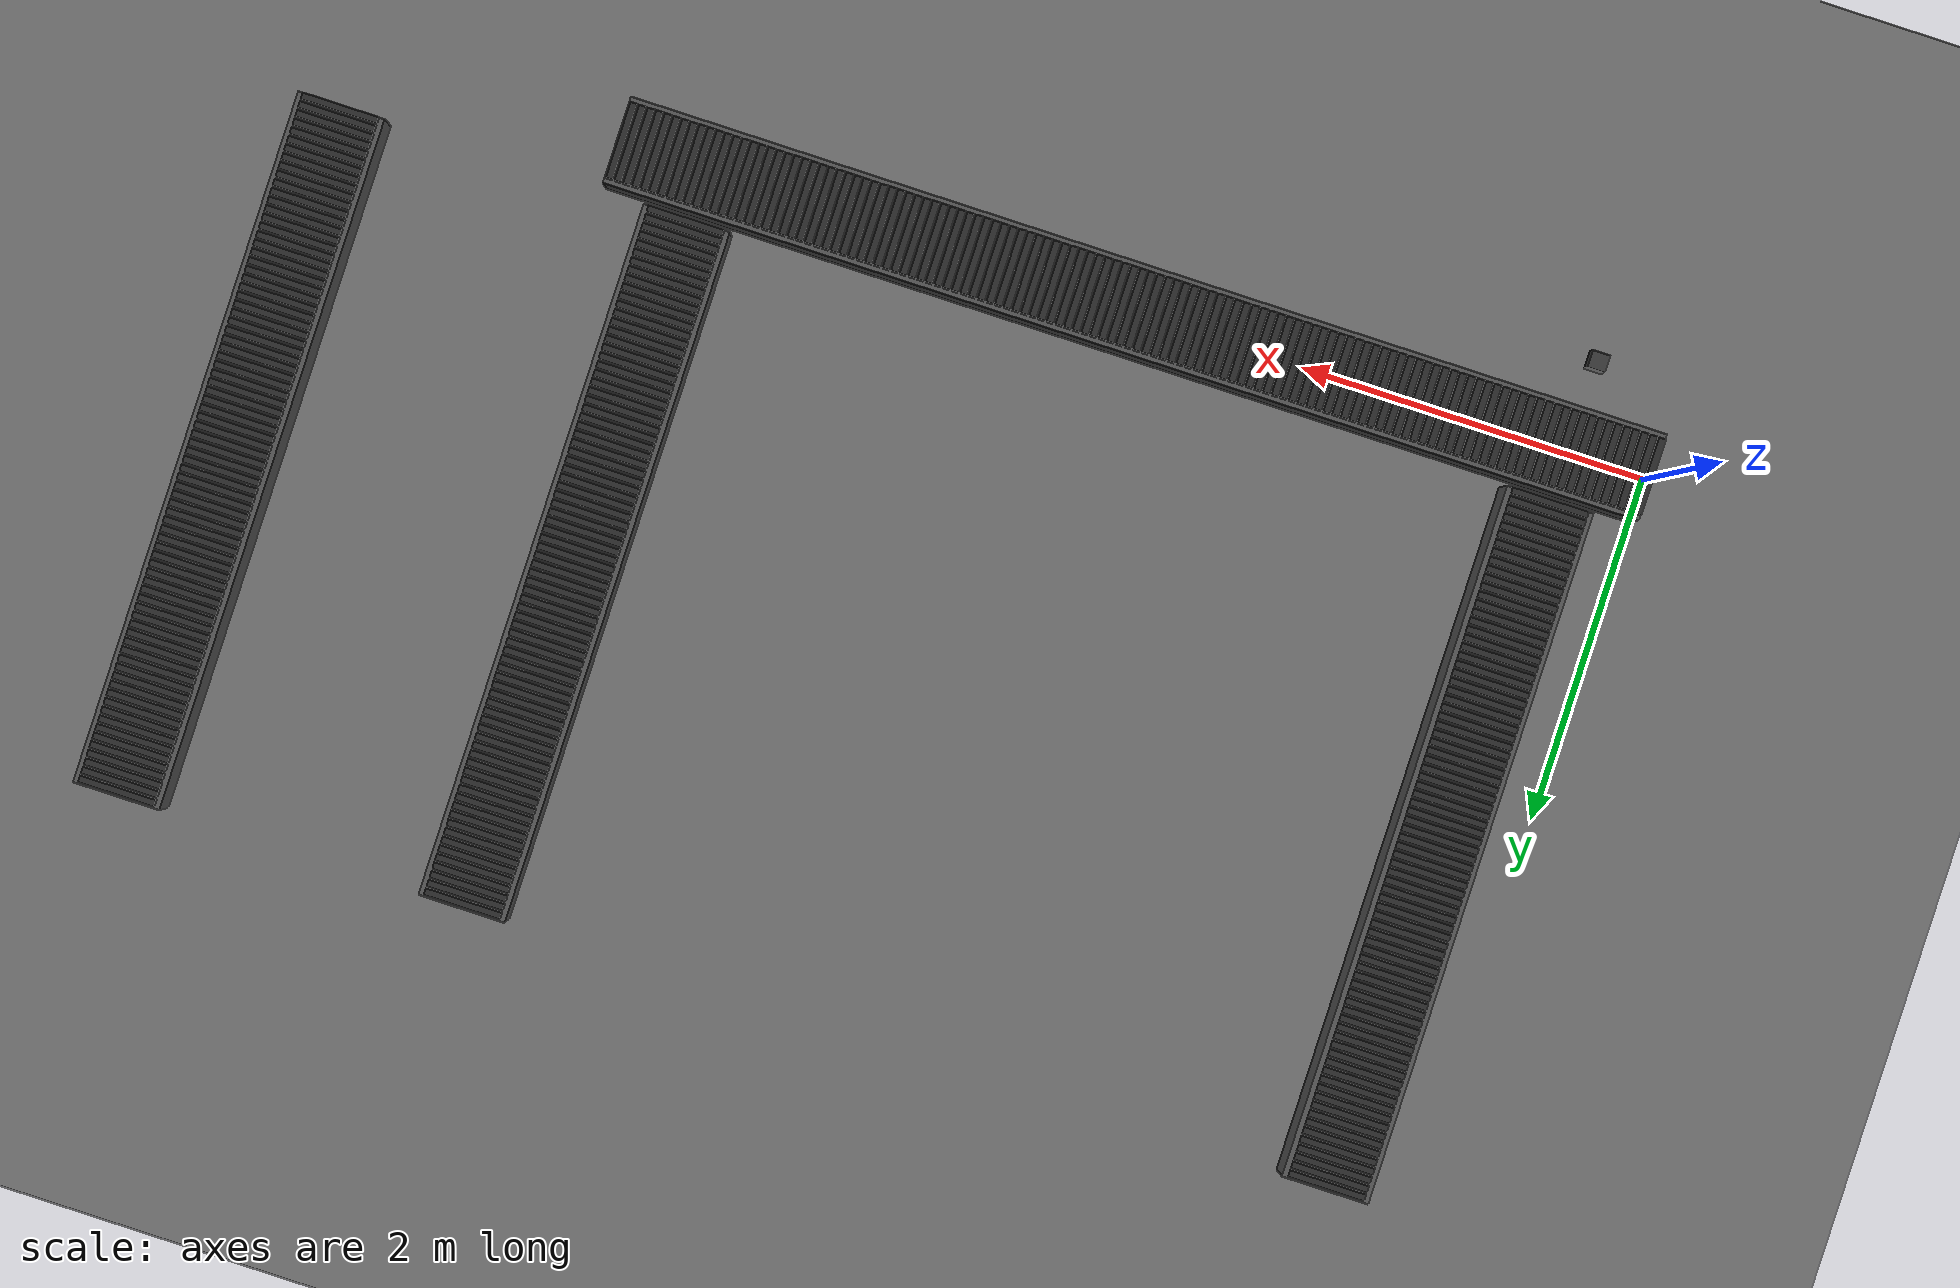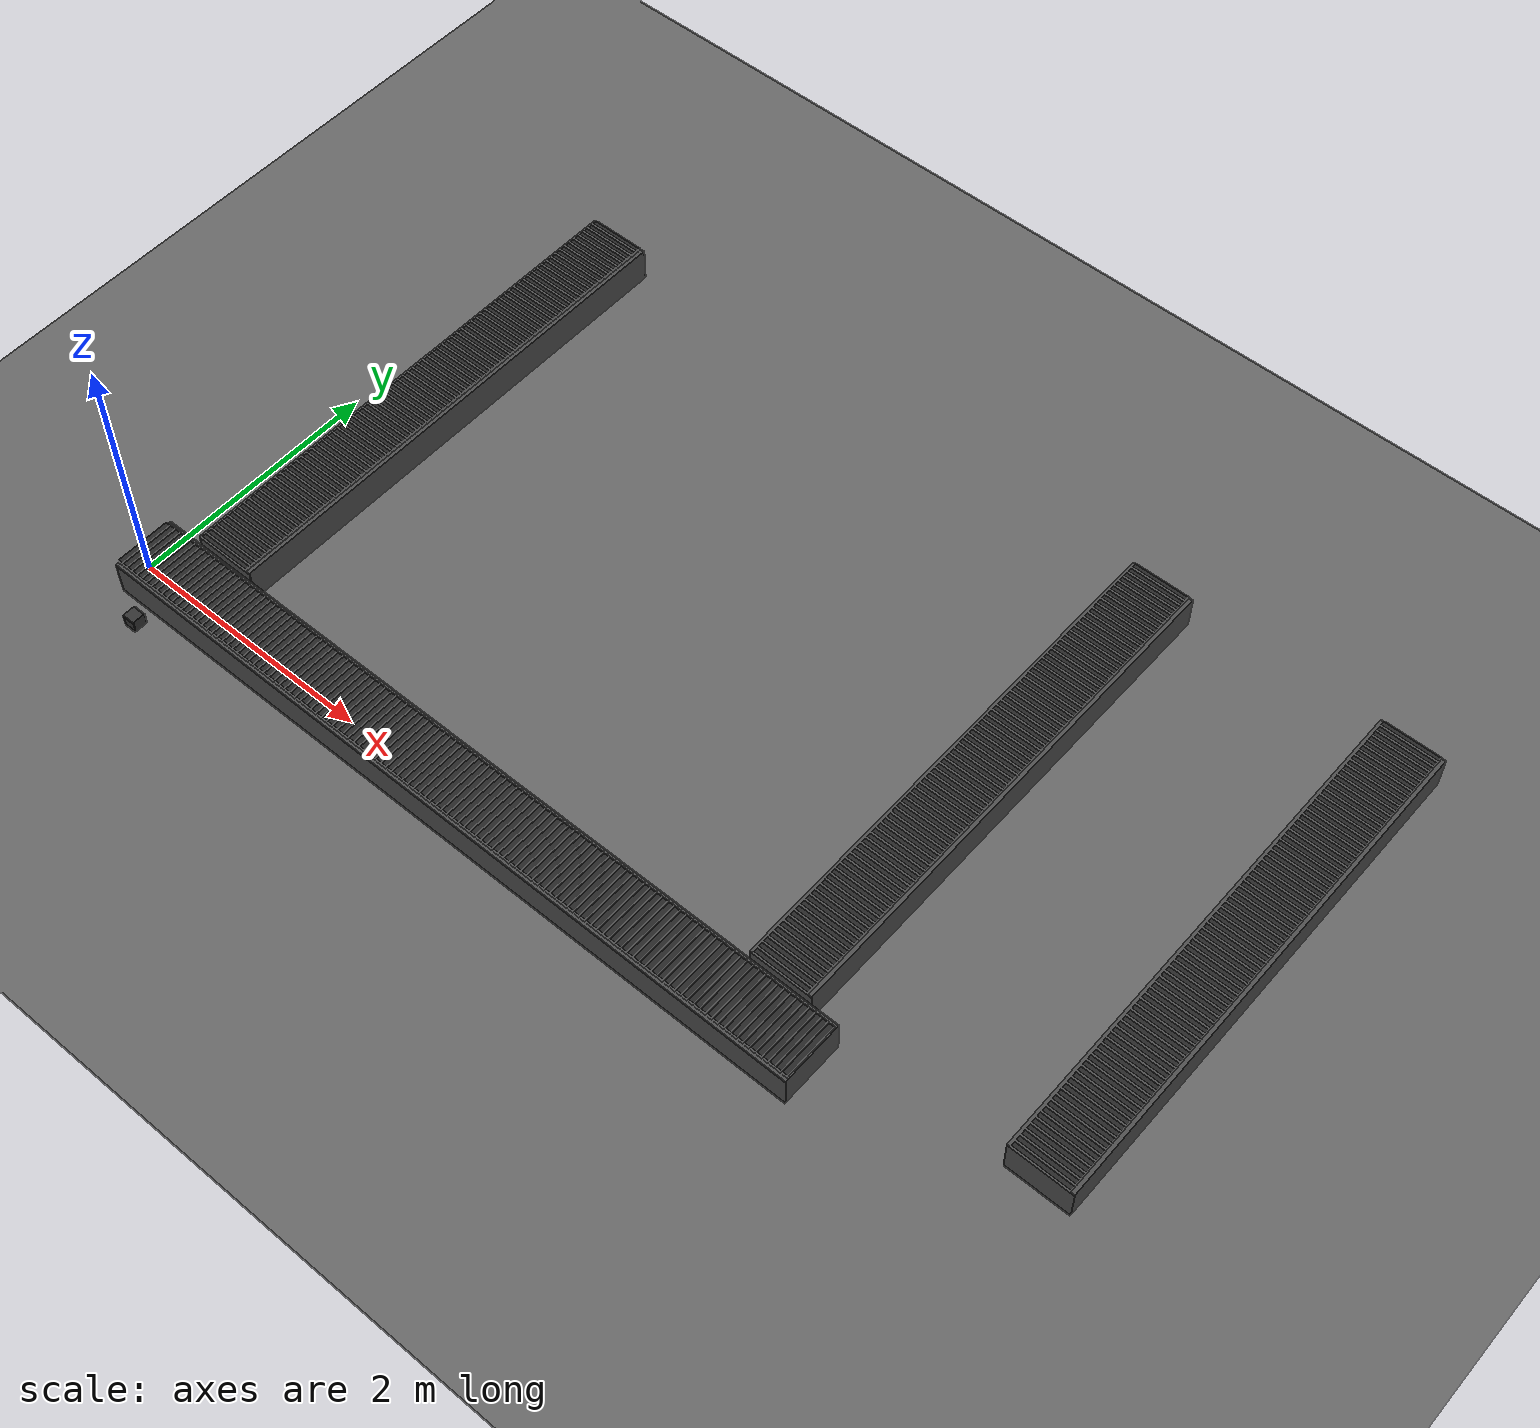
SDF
<sdf version="1.8">
 <world name="conveyor">
  <plugin filename="ignition-gazebo-physics-system" name="ignition::gazebo::systems::Physics"/>
  <plugin filename="ignition-gazebo-user-commands-system" name="ignition::gazebo::systems::UserCommands"/>
  <plugin filename="ignition-gazebo-scene-broadcaster-system" name="ignition::gazebo::systems::SceneBroadcaster"/>
  <plugin filename="ignition-gazebo-sensors-system" name="ignition::gazebo::systems::Sensors">
   <render_engine>ogre2</render_engine>
  </plugin>
  <physics name="default" type="ignored">
   <max_step_size>0.002</max_step_size>
   <real_time_factor>1.0</real_time_factor>
  </physics>
  <light type="directional" name="sun">
   <pose>0 0 10 0 0 0</pose>
   <diffuse>0.9 0.9 0.9 1</diffuse>
   <specular>0.3 0.3 0.3 1</specular>
   <direction>-0.5 0.1 -0.9</direction>
   <attenuation>
    <range>1000</range>
    <constant>0.9</constant>
    <linear>0.01</linear>
    <quadratic>0.001</quadratic>
   </attenuation>
  </light>
  <model name="ground_plane">
   <static>true</static>
   <link name="link">
    <collision name="col">
     <geometry><plane><normal>0 0 1</normal><size>50 50</size></plane></geometry>
     <surface><friction><ode><mu>1</mu><mu2>1</mu2></ode></friction></surface>
    </collision>
    <visual name="vis">
     <geometry><plane><normal>0 0 1</normal><size>50 50</size></plane></geometry>
     <material><ambient>0.4 0.4 0.4 1</ambient><diffuse>0.4 0.4 0.4 1</diffuse></material>
    </visual>
   </link>
  </model>
  <model name="overhead_camera">
   <static>true</static>
   <pose>0.5 -0.5 0.35 0 0 1.5708</pose>
   <link name="camera_link">
    <visual name="visual">
     <geometry><box><size>0.1 0.1 0.1</size></box></geometry>
     <material><ambient>0.2 0.2 0.2 1</ambient><diffuse>0.2 0.2 0.2 1</diffuse></material>
    </visual>
    <sensor name="overhead_cam" type="camera">
     <camera>
      <horizontal_fov>1.047</horizontal_fov>
      <image><width>1280</width><height>720</height><format>R8G8B8</format></image>
      <clip><near>0.1</near><far>10</far></clip>
     </camera>
     <always_on>1</always_on>
     <update_rate>30</update_rate>
     <visualize>true</visualize>
     <topic>/overhead_camera/image_raw</topic>
    </sensor>
   </link>
  </model>
  <model name="conveyor_belt_1">
   <include merge="true"><uri>package://sml_description/models/conveyor_belt_1</uri></include>
  </model>
  <model name="conveyor_belt_2">
   <include merge="true"><uri>package://sml_description/models/conveyor_belt_2</uri></include>
  </model>
  <model name="conveyor_belt_3">
   <pose>5.0 0 0 0 0 0</pose>
   <include merge="true"><uri>package://sml_description/models/conveyor_belt_3</uri></include>
  </model>
  <model name="conveyor_belt_4">
   <pose>7.0 0 0 0 0 0</pose>
   <include merge="true"><uri>package://sml_description/models/conveyor_belt_4</uri></include>
  </model>
 </world>
</sdf>

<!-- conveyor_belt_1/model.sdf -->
<sdf version="1.8">
  <model name="conveyor_belt">
    <!--
      InfiniteConveyor plugin — drives all slat joints and wraps them.
      Adjust belt_speed (m/s) to change conveyor speed.
    -->
    <plugin filename="InfiniteConveyorPlugin" name="conveyor::InfiniteConveyor">
      <belt_speed>-0.2</belt_speed>
      <end_x>4.32</end_x>
      <num_slats>80</num_slats>
      <slat_pitch>0.05</slat_pitch>
      <first_slat_x>0.31</first_slat_x>
      <slat_prefix>slat2</slat_prefix>
      <coordinate>y</coordinate>
      <cmd_vel_topic>/conveyor2/cmd_vel</cmd_vel_topic>
    </plugin>
      <model name="conveyor_frame_2">
    <self_collide>true</self_collide>
    <pose>0.5 0.29 0 0 0 1.5708</pose>
    <include merge="true">
      <uri>package://sml_description/models/conveyor_frame_4m</uri>
    </include>
  </model>
    <!-- Slat Models (using modular include) -->
    <model name="slat2_0">
      <pose>0.5 0.31 0.29 0 0 1.5708</pose>
      <include merge="true"><uri>package://sml_description/models/slat</uri></include>
      <joint name="slat2_0_joint" type="prismatic"><parent>world</parent><child>link</child><axis><xyz>1 0 0</xyz></axis></joint>
    </model>
    <model name="slat2_1">
      <pose>0.5 0.36 0.29 0 0 1.5708</pose>
      <include merge="true"><uri>package://sml_description/models/slat</uri></include>
      <joint name="slat2_1_joint" type="prismatic"><parent>world</parent><child>link</child><axis><xyz>1 0 0</xyz></axis></joint>
    </model>
    <model name="slat2_2">
      <pose>0.5 0.41 0.29 0 0 1.5708</pose>
      <include merge="true"><uri>package://sml_description/models/slat</uri></include>
      <joint name="slat2_2_joint" type="prismatic"><parent>world</parent><child>link</child><axis><xyz>1 0 0</xyz></axis></joint>
    </model>
    <model name="slat2_3">
      <pose>0.5 0.46 0.29 0 0 1.5708</pose>
      <include merge="true"><uri>package://sml_description/models/slat</uri></include>
      <joint name="slat2_3_joint" type="prismatic"><parent>world</parent><child>link</child><axis><xyz>1 0 0</xyz></axis></joint>
    </model>
    <model name="slat2_4">
      <pose>0.5 0.51 0.29 0 0 1.5708</pose>
      <include merge="true"><uri>package://sml_description/models/slat</uri></include>
      <joint name="slat2_4_joint" type="prismatic"><parent>world</parent><child>link</child><axis><xyz>1 0 0</xyz></axis></joint>
    </model>
    <model name="slat2_5">
      <pose>0.5 0.56 0.29 0 0 1.5708</pose>
      <include merge="true"><uri>package://sml_description/models/slat</uri></include>
      <joint name="slat2_5_joint" type="prismatic"><parent>world</parent><child>link</child><axis><xyz>1 0 0</xyz></axis></joint>
    </model>
    <model name="slat2_6">
      <pose>0.5 0.61 0.29 0 0 1.5708</pose>
      <include merge="true"><uri>package://sml_description/models/slat</uri></include>
      <joint name="slat2_6_joint" type="prismatic"><parent>world</parent><child>link</child><axis><xyz>1 0 0</xyz></axis></joint>
    </model>
    <model name="slat2_7">
      <pose>0.5 0.66 0.29 0 0 1.5708</pose>
      <include merge="true"><uri>package://sml_description/models/slat</uri></include>
      <joint name="slat2_7_joint" type="prismatic"><parent>world</parent><child>link</child><axis><xyz>1 0 0</xyz></axis></joint>
    </model>
    <model name="slat2_8">
      <pose>0.5 0.71 0.29 0 0 1.5708</pose>
      <include merge="true"><uri>package://sml_description/models/slat</uri></include>
      <joint name="slat2_8_joint" type="prismatic"><parent>world</parent><child>link</child><axis><xyz>1 0 0</xyz></axis></joint>
    </model>
    <model name="slat2_9">
      <pose>0.5 0.76 0.29 0 0 1.5708</pose>
      <include merge="true"><uri>package://sml_description/models/slat</uri></include>
      <joint name="slat2_9_joint" type="prismatic"><parent>world</parent><child>link</child><axis><xyz>1 0 0</xyz></axis></joint>
    </model>
    <model name="slat2_10">
      <pose>0.5 0.81 0.29 0 0 1.5708</pose>
      <include merge="true"><uri>package://sml_description/models/slat</uri></include>
      <joint name="slat2_10_joint" type="prismatic"><parent>world</parent><child>link</child><axis><xyz>1 0 0</xyz></axis></joint>
    </model>
    <model name="slat2_11">
      <pose>0.5 0.86 0.29 0 0 1.5708</pose>
      <include merge="true"><uri>package://sml_description/models/slat</uri></include>
      <joint name="slat2_11_joint" type="prismatic"><parent>world</parent><child>link</child><axis><xyz>1 0 0</xyz></axis></joint>
    </model>
    <model name="slat2_12">
      <pose>0.5 0.91 0.29 0 0 1.5708</pose>
      <include merge="true"><uri>package://sml_description/models/slat</uri></include>
      <joint name="slat2_12_joint" type="prismatic"><parent>world</parent><child>link</child><axis><xyz>1 0 0</xyz></axis></joint>
    </model>
    <model name="slat2_13">
      <pose>0.5 0.96 0.29 0 0 1.5708</pose>
      <include merge="true"><uri>package://sml_description/models/slat</uri></include>
      <joint name="slat2_13_joint" type="prismatic"><parent>world</parent><child>link</child><axis><xyz>1 0 0</xyz></axis></joint>
    </model>
    <model name="slat2_14">
      <pose>0.5 1.01 0.29 0 0 1.5708</pose>
      <include merge="true"><uri>package://sml_description/models/slat</uri></include>
      <joint name="slat2_14_joint" type="prismatic"><parent>world</parent><child>link</child><axis><xyz>1 0 0</xyz></axis></joint>
    </model>
    <model name="slat2_15">
      <pose>0.5 1.06 0.29 0 0 1.5708</pose>
      <include merge="true"><uri>package://sml_description/models/slat</uri></include>
      <joint name="slat2_15_joint" type="prismatic"><parent>world</parent><child>link</child><axis><xyz>1 0 0</xyz></axis></joint>
    </model>
    <model name="slat2_16">
      <pose>0.5 1.11 0.29 0 0 1.5708</pose>
      <include merge="true"><uri>package://sml_description/models/slat</uri></include>
      <joint name="slat2_16_joint" type="prismatic"><parent>world</parent><child>link</child><axis><xyz>1 0 0</xyz></axis></joint>
    </model>
    <model name="slat2_17">
      <pose>0.5 1.16 0.29 0 0 1.5708</pose>
      <include merge="true"><uri>package://sml_description/models/slat</uri></include>
      <joint name="slat2_17_joint" type="prismatic"><parent>world</parent><child>link</child><axis><xyz>1 0 0</xyz></axis></joint>
    </model>
    <model name="slat2_18">
      <pose>0.5 1.21 0.29 0 0 1.5708</pose>
      <include merge="true"><uri>package://sml_description/models/slat</uri></include>
      <joint name="slat2_18_joint" type="prismatic"><parent>world</parent><child>link</child><axis><xyz>1 0 0</xyz></axis></joint>
    </model>
    <model name="slat2_19">
      <pose>0.5 1.26 0.29 0 0 1.5708</pose>
      <include merge="true"><uri>package://sml_description/models/slat</uri></include>
      <joint name="slat2_19_joint" type="prismatic"><parent>world</parent><child>link</child><axis><xyz>1 0 0</xyz></axis></joint>
    </model>
    <model name="slat2_20">
      <pose>0.5 1.31 0.29 0 0 1.5708</pose>
      <include merge="true"><uri>package://sml_description/models/slat</uri></include>
      <joint name="slat2_20_joint" type="prismatic"><parent>world</parent><child>link</child><axis><xyz>1 0 0</xyz></axis></joint>
    </model>
    <model name="slat2_21">
      <pose>0.5 1.36 0.29 0 0 1.5708</pose>
      <include merge="true"><uri>package://sml_description/models/slat</uri></include>
      <joint name="slat2_21_joint" type="prismatic"><parent>world</parent><child>link</child><axis><xyz>1 0 0</xyz></axis></joint>
    </model>
    <model name="slat2_22">
      <pose>0.5 1.41 0.29 0 0 1.5708</pose>
      <include merge="true"><uri>package://sml_description/models/slat</uri></include>
      <joint name="slat2_22_joint" type="prismatic"><parent>world</parent><child>link</child><axis><xyz>1 0 0</xyz></axis></joint>
    </model>
    <model name="slat2_23">
      <pose>0.5 1.46 0.29 0 0 1.5708</pose>
      <include merge="true"><uri>package://sml_description/models/slat</uri></include>
      <joint name="slat2_23_joint" type="prismatic"><parent>world</parent><child>link</child><axis><xyz>1 0 0</xyz></axis></joint>
    </model>
    <model name="slat2_24">
      <pose>0.5 1.51 0.29 0 0 1.5708</pose>
      <include merge="true"><uri>package://sml_description/models/slat</uri></include>
      <joint name="slat2_24_joint" type="prismatic"><parent>world</parent><child>link</child><axis><xyz>1 0 0</xyz></axis></joint>
    </model>
    <model name="slat2_25">
      <pose>0.5 1.56 0.29 0 0 1.5708</pose>
      <include merge="true"><uri>package://sml_description/models/slat</uri></include>
      <joint name="slat2_25_joint" type="prismatic"><parent>world</parent><child>link</child><axis><xyz>1 0 0</xyz></axis></joint>
    </model>
    <model name="slat2_26">
      <pose>0.5 1.61 0.29 0 0 1.5708</pose>
      <include merge="true"><uri>package://sml_description/models/slat</uri></include>
      <joint name="slat2_26_joint" type="prismatic"><parent>world</parent><child>link</child><axis><xyz>1 0 0</xyz></axis></joint>
    </model>
    <model name="slat2_27">
      <pose>0.5 1.66 0.29 0 0 1.5708</pose>
      <include merge="true"><uri>package://sml_description/models/slat</uri></include>
      <joint name="slat2_27_joint" type="prismatic"><parent>world</parent><child>link</child><axis><xyz>1 0 0</xyz></axis></joint>
    </model>
    <model name="slat2_28">
      <pose>0.5 1.71 0.29 0 0 1.5708</pose>
      <include merge="true"><uri>package://sml_description/models/slat</uri></include>
      <joint name="slat2_28_joint" type="prismatic"><parent>world</parent><child>link</child><axis><xyz>1 0 0</xyz></axis></joint>
    </model>
    <model name="slat2_29">
      <pose>0.5 1.76 0.29 0 0 1.5708</pose>
      <include merge="true"><uri>package://sml_description/models/slat</uri></include>
      <joint name="slat2_29_joint" type="prismatic"><parent>world</parent><child>link</child><axis><xyz>1 0 0</xyz></axis></joint>
    </model>
    <model name="slat2_30">
      <pose>0.5 1.81 0.29 0 0 1.5708</pose>
      <include merge="true"><uri>package://sml_description/models/slat</uri></include>
      <joint name="slat2_30_joint" type="prismatic"><parent>world</parent><child>link</child><axis><xyz>1 0 0</xyz></axis></joint>
    </model>
    <model name="slat2_31">
      <pose>0.5 1.86 0.29 0 0 1.5708</pose>
      <include merge="true"><uri>package://sml_description/models/slat</uri></include>
      <joint name="slat2_31_joint" type="prismatic"><parent>world</parent><child>link</child><axis><xyz>1 0 0</xyz></axis></joint>
    </model>
    <model name="slat2_32">
      <pose>0.5 1.91 0.29 0 0 1.5708</pose>
      <include merge="true"><uri>package://sml_description/models/slat</uri></include>
      <joint name="slat2_32_joint" type="prismatic"><parent>world</parent><child>link</child><axis><xyz>1 0 0</xyz></axis></joint>
    </model>
    <model name="slat2_33">
      <pose>0.5 1.96 0.29 0 0 1.5708</pose>
      <include merge="true"><uri>package://sml_description/models/slat</uri></include>
      <joint name="slat2_33_joint" type="prismatic"><parent>world</parent><child>link</child><axis><xyz>1 0 0</xyz></axis></joint>
    </model>
    <model name="slat2_34">
      <pose>0.5 2.01 0.29 0 0 1.5708</pose>
      <include merge="true"><uri>package://sml_description/models/slat</uri></include>
      <joint name="slat2_34_joint" type="prismatic"><parent>world</parent><child>link</child><axis><xyz>1 0 0</xyz></axis></joint>
    </model>
    <model name="slat2_35">
      <pose>0.5 2.06 0.29 0 0 1.5708</pose>
      <include merge="true"><uri>package://sml_description/models/slat</uri></include>
      <joint name="slat2_35_joint" type="prismatic"><parent>world</parent><child>link</child><axis><xyz>1 0 0</xyz></axis></joint>
    </model>
    <model name="slat2_36">
      <pose>0.5 2.11 0.29 0 0 1.5708</pose>
      <include merge="true"><uri>package://sml_description/models/slat</uri></include>
      <joint name="slat2_36_joint" type="prismatic"><parent>world</parent><child>link</child><axis><xyz>1 0 0</xyz></axis></joint>
    </model>
    <model name="slat2_37">
      <pose>0.5 2.16 0.29 0 0 1.5708</pose>
      <include merge="true"><uri>package://sml_description/models/slat</uri></include>
      <joint name="slat2_37_joint" type="prismatic"><parent>world</parent><child>link</child><axis><xyz>1 0 0</xyz></axis></joint>
    </model>
    <model name="slat2_38">
      <pose>0.5 2.21 0.29 0 0 1.5708</pose>
      <include merge="true"><uri>package://sml_description/models/slat</uri></include>
      <joint name="slat2_38_joint" type="prismatic"><parent>world</parent><child>link</child><axis><xyz>1 0 0</xyz></axis></joint>
    </model>
    <model name="slat2_39">
      <pose>0.5 2.26 0.29 0 0 1.5708</pose>
      <include merge="true"><uri>package://sml_description/models/slat</uri></include>
      <joint name="slat2_39_joint" type="prismatic"><parent>world</parent><child>link</child><axis><xyz>1 0 0</xyz></axis></joint>
    </model>
    <model name="slat2_40">
      <pose>0.5 2.31 0.29 0 0 1.5708</pose>
      <include merge="true"><uri>package://sml_description/models/slat</uri></include>
      <joint name="slat2_40_joint" type="prismatic"><parent>world</parent><child>link</child><axis><xyz>1 0 0</xyz></axis></joint>
    </model>
    <model name="slat2_41">
      <pose>0.5 2.36 0.29 0 0 1.5708</pose>
      <include merge="true"><uri>package://sml_description/models/slat</uri></include>
      <joint name="slat2_41_joint" type="prismatic"><parent>world</parent><child>link</child><axis><xyz>1 0 0</xyz></axis></joint>
    </model>
    <model name="slat2_42">
      <pose>0.5 2.41 0.29 0 0 1.5708</pose>
      <include merge="true"><uri>package://sml_description/models/slat</uri></include>
      <joint name="slat2_42_joint" type="prismatic"><parent>world</parent><child>link</child><axis><xyz>1 0 0</xyz></axis></joint>
    </model>
    <model name="slat2_43">
      <pose>0.5 2.46 0.29 0 0 1.5708</pose>
      <include merge="true"><uri>package://sml_description/models/slat</uri></include>
      <joint name="slat2_43_joint" type="prismatic"><parent>world</parent><child>link</child><axis><xyz>1 0 0</xyz></axis></joint>
    </model>
    <model name="slat2_44">
      <pose>0.5 2.51 0.29 0 0 1.5708</pose>
      <include merge="true"><uri>package://sml_description/models/slat</uri></include>
      <joint name="slat2_44_joint" type="prismatic"><parent>world</parent><child>link</child><axis><xyz>1 0 0</xyz></axis></joint>
    </model>
    <model name="slat2_45">
      <pose>0.5 2.56 0.29 0 0 1.5708</pose>
      <include merge="true"><uri>package://sml_description/models/slat</uri></include>
      <joint name="slat2_45_joint" type="prismatic"><parent>world</parent><child>link</child><axis><xyz>1 0 0</xyz></axis></joint>
    </model>
    <model name="slat2_46">
      <pose>0.5 2.61 0.29 0 0 1.5708</pose>
      <include merge="true"><uri>package://sml_description/models/slat</uri></include>
      <joint name="slat2_46_joint" type="prismatic"><parent>world</parent><child>link</child><axis><xyz>1 0 0</xyz></axis></joint>
    </model>
    <model name="slat2_47">
      <pose>0.5 2.66 0.29 0 0 1.5708</pose>
      <include merge="true"><uri>package://sml_description/models/slat</uri></include>
      <joint name="slat2_47_joint" type="prismatic"><parent>world</parent><child>link</child><axis><xyz>1 0 0</xyz></axis></joint>
    </model>
    <model name="slat2_48">
      <pose>0.5 2.71 0.29 0 0 1.5708</pose>
      <include merge="true"><uri>package://sml_description/models/slat</uri></include>
      <joint name="slat2_48_joint" type="prismatic"><parent>world</parent><child>link</child><axis><xyz>1 0 0</xyz></axis></joint>
    </model>
    <model name="slat2_49">
      <pose>0.5 2.76 0.29 0 0 1.5708</pose>
      <include merge="true"><uri>package://sml_description/models/slat</uri></include>
      <joint name="slat2_49_joint" type="prismatic"><parent>world</parent><child>link</child><axis><xyz>1 0 0</xyz></axis></joint>
    </model>
    <model name="slat2_50">
      <pose>0.5 2.81 0.29 0 0 1.5708</pose>
      <include merge="true"><uri>package://sml_description/models/slat</uri></include>
      <joint name="slat2_50_joint" type="prismatic"><parent>world</parent><child>link</child><axis><xyz>1 0 0</xyz></axis></joint>
    </model>
    <model name="slat2_51">
      <pose>0.5 2.86 0.29 0 0 1.5708</pose>
      <include merge="true"><uri>package://sml_description/models/slat</uri></include>
      <joint name="slat2_51_joint" type="prismatic"><parent>world</parent><child>link</child><axis><xyz>1 0 0</xyz></axis></joint>
    </model>
    <model name="slat2_52">
      <pose>0.5 2.91 0.29 0 0 1.5708</pose>
      <include merge="true"><uri>package://sml_description/models/slat</uri></include>
      <joint name="slat2_52_joint" type="prismatic"><parent>world</parent><child>link</child><axis><xyz>1 0 0</xyz></axis></joint>
    </model>
    <model name="slat2_53">
      <pose>0.5 2.96 0.29 0 0 1.5708</pose>
      <include merge="true"><uri>package://sml_description/models/slat</uri></include>
      <joint name="slat2_53_joint" type="prismatic"><parent>world</parent><child>link</child><axis><xyz>1 0 0</xyz></axis></joint>
    </model>
    <model name="slat2_54">
      <pose>0.5 3.01 0.29 0 0 1.5708</pose>
      <include merge="true"><uri>package://sml_description/models/slat</uri></include>
      <joint name="slat2_54_joint" type="prismatic"><parent>world</parent><child>link</child><axis><xyz>1 0 0</xyz></axis></joint>
    </model>
    <model name="slat2_55">
      <pose>0.5 3.06 0.29 0 0 1.5708</pose>
      <include merge="true"><uri>package://sml_description/models/slat</uri></include>
      <joint name="slat2_55_joint" type="prismatic"><parent>world</parent><child>link</child><axis><xyz>1 0 0</xyz></axis></joint>
    </model>
    <model name="slat2_56">
      <pose>0.5 3.11 0.29 0 0 1.5708</pose>
      <include merge="true"><uri>package://sml_description/models/slat</uri></include>
      <joint name="slat2_56_joint" type="prismatic"><parent>world</parent><child>link</child><axis><xyz>1 0 0</xyz></axis></joint>
    </model>
    <model name="slat2_57">
      <pose>0.5 3.16 0.29 0 0 1.5708</pose>
      <include merge="true"><uri>package://sml_description/models/slat</uri></include>
      <joint name="slat2_57_joint" type="prismatic"><parent>world</parent><child>link</child><axis><xyz>1 0 0</xyz></axis></joint>
    </model>
    <model name="slat2_58">
      <pose>0.5 3.21 0.29 0 0 1.5708</pose>
      <include merge="true"><uri>package://sml_description/models/slat</uri></include>
      <joint name="slat2_58_joint" type="prismatic"><parent>world</parent><child>link</child><axis><xyz>1 0 0</xyz></axis></joint>
    </model>
    <model name="slat2_59">
      <pose>0.5 3.26 0.29 0 0 1.5708</pose>
      <include merge="true"><uri>package://sml_description/models/slat</uri></include>
      <joint name="slat2_59_joint" type="prismatic"><parent>world</parent><child>link</child><axis><xyz>1 0 0</xyz></axis></joint>
    </model>
    <model name="slat2_60">
      <pose>0.5 3.31 0.29 0 0 1.5708</pose>
      <include merge="true"><uri>package://sml_description/models/slat</uri></include>
      <joint name="slat2_60_joint" type="prismatic"><parent>world</parent><child>link</child><axis><xyz>1 0 0</xyz></axis></joint>
    </model>
    <model name="slat2_61">
      <pose>0.5 3.36 0.29 0 0 1.5708</pose>
      <include merge="true"><uri>package://sml_description/models/slat</uri></include>
      <joint name="slat2_61_joint" type="prismatic"><parent>world</parent><child>link</child><axis><xyz>1 0 0</xyz></axis></joint>
    </model>
    <model name="slat2_62">
      <pose>0.5 3.41 0.29 0 0 1.5708</pose>
      <include merge="true"><uri>package://sml_description/models/slat</uri></include>
      <joint name="slat2_62_joint" type="prismatic"><parent>world</parent><child>link</child><axis><xyz>1 0 0</xyz></axis></joint>
    </model>
    <model name="slat2_63">
      <pose>0.5 3.46 0.29 0 0 1.5708</pose>
      <include merge="true"><uri>package://sml_description/models/slat</uri></include>
      <joint name="slat2_63_joint" type="prismatic"><parent>world</parent><child>link</child><axis><xyz>1 0 0</xyz></axis></joint>
    </model>
    <model name="slat2_64">
      <pose>0.5 3.51 0.29 0 0 1.5708</pose>
      <include merge="true"><uri>package://sml_description/models/slat</uri></include>
      <joint name="slat2_64_joint" type="prismatic"><parent>world</parent><child>link</child><axis><xyz>1 0 0</xyz></axis></joint>
    </model>
    <model name="slat2_65">
      <pose>0.5 3.56 0.29 0 0 1.5708</pose>
      <include merge="true"><uri>package://sml_description/models/slat</uri></include>
      <joint name="slat2_65_joint" type="prismatic"><parent>world</parent><child>link</child><axis><xyz>1 0 0</xyz></axis></joint>
    </model>
    <model name="slat2_66">
      <pose>0.5 3.61 0.29 0 0 1.5708</pose>
      <include merge="true"><uri>package://sml_description/models/slat</uri></include>
      <joint name="slat2_66_joint" type="prismatic"><parent>world</parent><child>link</child><axis><xyz>1 0 0</xyz></axis></joint>
    </model>
    <model name="slat2_67">
      <pose>0.5 3.66 0.29 0 0 1.5708</pose>
      <include merge="true"><uri>package://sml_description/models/slat</uri></include>
      <joint name="slat2_67_joint" type="prismatic"><parent>world</parent><child>link</child><axis><xyz>1 0 0</xyz></axis></joint>
    </model>
    <model name="slat2_68">
      <pose>0.5 3.71 0.29 0 0 1.5708</pose>
      <include merge="true"><uri>package://sml_description/models/slat</uri></include>
      <joint name="slat2_68_joint" type="prismatic"><parent>world</parent><child>link</child><axis><xyz>1 0 0</xyz></axis></joint>
    </model>
    <model name="slat2_69">
      <pose>0.5 3.76 0.29 0 0 1.5708</pose>
      <include merge="true"><uri>package://sml_description/models/slat</uri></include>
      <joint name="slat2_69_joint" type="prismatic"><parent>world</parent><child>link</child><axis><xyz>1 0 0</xyz></axis></joint>
    </model>
    <model name="slat2_70">
      <pose>0.5 3.81 0.29 0 0 1.5708</pose>
      <include merge="true"><uri>package://sml_description/models/slat</uri></include>
      <joint name="slat2_70_joint" type="prismatic"><parent>world</parent><child>link</child><axis><xyz>1 0 0</xyz></axis></joint>
    </model>
    <model name="slat2_71">
      <pose>0.5 3.86 0.29 0 0 1.5708</pose>
      <include merge="true"><uri>package://sml_description/models/slat</uri></include>
      <joint name="slat2_71_joint" type="prismatic"><parent>world</parent><child>link</child><axis><xyz>1 0 0</xyz></axis></joint>
    </model>
    <model name="slat2_72">
      <pose>0.5 3.91 0.29 0 0 1.5708</pose>
      <include merge="true"><uri>package://sml_description/models/slat</uri></include>
      <joint name="slat2_72_joint" type="prismatic"><parent>world</parent><child>link</child><axis><xyz>1 0 0</xyz></axis></joint>
    </model>
    <model name="slat2_73">
      <pose>0.5 3.96 0.29 0 0 1.5708</pose>
      <include merge="true"><uri>package://sml_description/models/slat</uri></include>
      <joint name="slat2_73_joint" type="prismatic"><parent>world</parent><child>link</child><axis><xyz>1 0 0</xyz></axis></joint>
    </model>
    <model name="slat2_74">
      <pose>0.5 4.01 0.29 0 0 1.5708</pose>
      <include merge="true"><uri>package://sml_description/models/slat</uri></include>
      <joint name="slat2_74_joint" type="prismatic"><parent>world</parent><child>link</child><axis><xyz>1 0 0</xyz></axis></joint>
    </model>
    <model name="slat2_75">
      <pose>0.5 4.06 0.29 0 0 1.5708</pose>
      <include merge="true"><uri>package://sml_description/models/slat</uri></include>
      <joint name="slat2_75_joint" type="prismatic"><parent>world</parent><child>link</child><axis><xyz>1 0 0</xyz></axis></joint>
    </model>
    <model name="slat2_76">
      <pose>0.5 4.11 0.29 0 0 1.5708</pose>
      <include merge="true"><uri>package://sml_description/models/slat</uri></include>
      <joint name="slat2_76_joint" type="prismatic"><parent>world</parent><child>link</child><axis><xyz>1 0 0</xyz></axis></joint>
    </model>
    <model name="slat2_77">
      <pose>0.5 4.16 0.29 0 0 1.5708</pose>
      <include merge="true"><uri>package://sml_description/models/slat</uri></include>
      <joint name="slat2_77_joint" type="prismatic"><parent>world</parent><child>link</child><axis><xyz>1 0 0</xyz></axis></joint>
    </model>
    <model name="slat2_78">
      <pose>0.5 4.21 0.29 0 0 1.5708</pose>
      <include merge="true"><uri>package://sml_description/models/slat</uri></include>
      <joint name="slat2_78_joint" type="prismatic"><parent>world</parent><child>link</child><axis><xyz>1 0 0</xyz></axis></joint>
    </model>
    <model name="slat2_79">
      <pose>0.5 4.26 0.29 0 0 1.5708</pose>
      <include merge="true"><uri>package://sml_description/models/slat</uri></include>
      <joint name="slat2_79_joint" type="prismatic"><parent>world</parent><child>link</child><axis><xyz>1 0 0</xyz></axis></joint>
    </model>
  </model>
</sdf>

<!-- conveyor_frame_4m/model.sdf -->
<sdf version="1.8">
<model name="conveyor_frame_4m">
    <static>true</static>
    <pose>2.0 0 0.14 0 0 0</pose>
    <link name="link">
      <inertial><mass>400000</mass>
        <inertia><ixx>4e6</ixx><ixy>0</ixy><ixz>0</ixz>
                 <iyy>4e6</iyy><iyz>0</iyz><izz>4e6</izz></inertia>
      </inertial>

      <!-- Main body (4.0m long) -->
      <collision name="frame_col">
        <geometry><box><size>4.0 0.5 0.28</size></box></geometry>
      </collision>
      <visual name="frame_vis">
        <geometry><box><size>4.0 0.5 0.28</size></box></geometry>
        <material>
          <ambient>0.28 0.28 0.28 1</ambient>
          <diffuse>0.30 0.30 0.30 1</diffuse>
          <specular>0.5 0.5 0.5 1</specular>
        </material>
      </visual>

      <!-- Legs (every 1m approx) -->
      <visual name="leg_1l"><pose>-1.96  0.21 -0.14 0 0 0</pose>
        <geometry><box><size>0.04 0.04 0.28</size></box></geometry>
        <material><ambient>0.2 0.2 0.2 1</ambient><diffuse>0.2 0.2 0.2 1</diffuse></material></visual>
      <visual name="leg_1r"><pose>-1.96 -0.21 -0.14 0 0 0</pose>
        <geometry><box><size>0.04 0.04 0.28</size></box></geometry>
        <material><ambient>0.2 0.2 0.2 1</ambient><diffuse>0.2 0.2 0.2 1</diffuse></material></visual>

      <visual name="leg_2l"><pose>-1.0   0.21 -0.14 0 0 0</pose>
        <geometry><box><size>0.04 0.04 0.28</size></box></geometry>
        <material><ambient>0.2 0.2 0.2 1</ambient><diffuse>0.2 0.2 0.2 1</diffuse></material></visual>
      <visual name="leg_2r"><pose>-1.0  -0.21 -0.14 0 0 0</pose>
        <geometry><box><size>0.04 0.04 0.28</size></box></geometry>
        <material><ambient>0.2 0.2 0.2 1</ambient><diffuse>0.2 0.2 0.2 1</diffuse></material></visual>

      <visual name="leg_3l"><pose> 0.0   0.21 -0.14 0 0 0</pose>
        <geometry><box><size>0.04 0.04 0.28</size></box></geometry>
        <material><ambient>0.2 0.2 0.2 1</ambient><diffuse>0.2 0.2 0.2 1</diffuse></material></visual>
      <visual name="leg_3r"><pose> 0.0  -0.21 -0.14 0 0 0</pose>
        <geometry><box><size>0.04 0.04 0.28</size></box></geometry>
        <material><ambient>0.2 0.2 0.2 1</ambient><diffuse>0.2 0.2 0.2 1</diffuse></material></visual>

      <visual name="leg_4l"><pose> 1.0   0.21 -0.14 0 0 0</pose>
        <geometry><box><size>0.04 0.04 0.28</size></box></geometry>
        <material><ambient>0.2 0.2 0.2 1</ambient><diffuse>0.2 0.2 0.2 1</diffuse></material></visual>
      <visual name="leg_4r"><pose> 1.0  -0.21 -0.14 0 0 0</pose>
        <geometry><box><size>0.04 0.04 0.28</size></box></geometry>
        <material><ambient>0.2 0.2 0.2 1</ambient><diffuse>0.2 0.2 0.2 1</diffuse></material></visual>

      <visual name="leg_5l"><pose> 1.96  0.21 -0.14 0 0 0</pose>
        <geometry><box><size>0.04 0.04 0.28</size></box></geometry>
        <material><ambient>0.2 0.2 0.2 1</ambient><diffuse>0.2 0.2 0.2 1</diffuse></material></visual>
      <visual name="leg_5r"><pose> 1.96 -0.21 -0.14 0 0 0</pose>
        <geometry><box><size>0.04 0.04 0.28</size></box></geometry>
        <material><ambient>0.2 0.2 0.2 1</ambient><diffuse>0.2 0.2 0.2 1</diffuse></material></visual>

      <!-- Cross beams -->
      <visual name="beam_1"><pose>-1.96 0 -0.10 0 0 0</pose>
        <geometry><box><size>0.04 0.46 0.04</size></box></geometry>
        <material><ambient>0.2 0.2 0.2 1</ambient><diffuse>0.2 0.2 0.2 1</diffuse></material></visual>
      <visual name="beam_2"><pose>-1.0 0 -0.10 0 0 0</pose>
        <geometry><box><size>0.04 0.46 0.04</size></box></geometry>
        <material><ambient>0.2 0.2 0.2 1</ambient><diffuse>0.2 0.2 0.2 1</diffuse></material></visual>
      <visual name="beam_3"><pose>0 0 -0.10 0 0 0</pose>
        <geometry><box><size>0.04 0.46 0.04</size></box></geometry>
        <material><ambient>0.2 0.2 0.2 1</ambient><diffuse>0.2 0.2 0.2 1</diffuse></material></visual>
      <visual name="beam_4"><pose>1.0 0 -0.10 0 0 0</pose>
        <geometry><box><size>0.04 0.46 0.04</size></box></geometry>
        <material><ambient>0.2 0.2 0.2 1</ambient><diffuse>0.2 0.2 0.2 1</diffuse></material></visual>
      <visual name="beam_5"><pose>1.96 0 -0.10 0 0 0</pose>
        <geometry><box><size>0.04 0.46 0.04</size></box></geometry>
        <material><ambient>0.2 0.2 0.2 1</ambient><diffuse>0.2 0.2 0.2 1</diffuse></material></visual>
    </link>
  </model>
</sdf>

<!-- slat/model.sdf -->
<sdf version="1.8">
  <model name="slat">
    <link name="link">
      <inertial>
        <mass>0.3</mass>
        <inertia>
          <ixx>0.004867</ixx>
          <ixy>0</ixy>
          <ixz>0</ixz>
          <iyy>0.000050</iyy>
          <iyz>0</iyz>
          <izz>0.004883</izz>
        </inertia>
      </inertial>

      <collision name="collision">
        <geometry>
          <box>
            <size>0.04 0.44 0.02</size>
          </box>
        </geometry>
        <surface>
          <friction>
            <ode>
              <mu>8.0</mu>
              <mu2>8.0</mu2>
              <fdir1>1 0 0</fdir1>
            </ode>
          </friction>
          <contact>
            <ode>
              <kp>1e6</kp>
              <kd>10</kd>
              <min_depth>0.001</min_depth>
            </ode>
          </contact>
        </surface>
      </collision>

      <visual name="visual">
        <geometry>
          <box>
            <size>0.04 0.44 0.02</size>
          </box>
        </geometry>
        <material>
          <ambient>0.15 0.15 0.15 1</ambient>
          <diffuse>0.15 0.15 0.15 1</diffuse>
          <specular>0.2 0.2 0.2 1</specular>
        </material>
      </visual>
    </link>
  </model>
</sdf>

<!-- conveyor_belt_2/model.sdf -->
<sdf version="1.8">
  <model name="conveyor_belt">

    <model name="conveyor_frame">
    <self_collide>true</self_collide>
    <pose>0 0 0 0 0 0</pose>
    <include merge="true">
      <uri>package://sml_description/models/conveyor_frame_6m</uri>
    </include>
    </model>

    <plugin filename="InfiniteConveyorPlugin" name="conveyor::InfiniteConveyor">
      <belt_speed>0.2</belt_speed>
      <end_x>6.02</end_x>
      <num_slats>120</num_slats>
      <slat_pitch>0.05</slat_pitch>
      <first_slat_x>0.02</first_slat_x>
      <slat_prefix>slat</slat_prefix>
      <cmd_vel_topic>/conveyor/cmd_vel</cmd_vel_topic>
    </plugin>

  <model name="slat_0">
    <pose>0.02 0 0.29 0 0 0</pose>
    <include merge="true"><uri>package://sml_description/models/slat</uri></include>
    <joint name="slat_0_joint" type="prismatic"><parent>world</parent><child>link</child><axis><xyz>1 0 0</xyz><limit><lower>-1e9</lower><upper>1e9</upper><effort>1e9</effort><velocity>10</velocity></limit></axis></joint>
  </model>
  <model name="slat_1">
    <pose>0.07 0 0.29 0 0 0</pose>
    <include merge="true"><uri>package://sml_description/models/slat</uri></include>
    <joint name="slat_1_joint" type="prismatic"><parent>world</parent><child>link</child><axis><xyz>1 0 0</xyz><limit><lower>-1e9</lower><upper>1e9</upper><effort>1e9</effort><velocity>10</velocity></limit></axis></joint>
  </model>
  <model name="slat_2">
    <pose>0.12 0 0.29 0 0 0</pose>
    <include merge="true"><uri>package://sml_description/models/slat</uri></include>
    <joint name="slat_2_joint" type="prismatic"><parent>world</parent><child>link</child><axis><xyz>1 0 0</xyz><limit><lower>-1e9</lower><upper>1e9</upper><effort>1e9</effort><velocity>10</velocity></limit></axis></joint>
  </model>
  <model name="slat_3">
    <pose>0.17 0 0.29 0 0 0</pose>
    <include merge="true"><uri>package://sml_description/models/slat</uri></include>
    <joint name="slat_3_joint" type="prismatic"><parent>world</parent><child>link</child><axis><xyz>1 0 0</xyz><limit><lower>-1e9</lower><upper>1e9</upper><effort>1e9</effort><velocity>10</velocity></limit></axis></joint>
  </model>
  <model name="slat_4">
    <pose>0.22 0 0.29 0 0 0</pose>
    <include merge="true"><uri>package://sml_description/models/slat</uri></include>
    <joint name="slat_4_joint" type="prismatic"><parent>world</parent><child>link</child><axis><xyz>1 0 0</xyz><limit><lower>-1e9</lower><upper>1e9</upper><effort>1e9</effort><velocity>10</velocity></limit></axis></joint>
  </model>
  <model name="slat_5">
    <pose>0.27 0 0.29 0 0 0</pose>
    <include merge="true"><uri>package://sml_description/models/slat</uri></include>
    <joint name="slat_5_joint" type="prismatic"><parent>world</parent><child>link</child><axis><xyz>1 0 0</xyz><limit><lower>-1e9</lower><upper>1e9</upper><effort>1e9</effort><velocity>10</velocity></limit></axis></joint>
  </model>
  <model name="slat_6">
    <pose>0.32 0 0.29 0 0 0</pose>
    <include merge="true"><uri>package://sml_description/models/slat</uri></include>
    <joint name="slat_6_joint" type="prismatic"><parent>world</parent><child>link</child><axis><xyz>1 0 0</xyz><limit><lower>-1e9</lower><upper>1e9</upper><effort>1e9</effort><velocity>10</velocity></limit></axis></joint>
  </model>
  <model name="slat_7">
    <pose>0.37 0 0.29 0 0 0</pose>
    <include merge="true"><uri>package://sml_description/models/slat</uri></include>
    <joint name="slat_7_joint" type="prismatic"><parent>world</parent><child>link</child><axis><xyz>1 0 0</xyz><limit><lower>-1e9</lower><upper>1e9</upper><effort>1e9</effort><velocity>10</velocity></limit></axis></joint>
  </model>
  <model name="slat_8">
    <pose>0.42 0 0.29 0 0 0</pose>
    <include merge="true"><uri>package://sml_description/models/slat</uri></include>
    <joint name="slat_8_joint" type="prismatic"><parent>world</parent><child>link</child><axis><xyz>1 0 0</xyz><limit><lower>-1e9</lower><upper>1e9</upper><effort>1e9</effort><velocity>10</velocity></limit></axis></joint>
  </model>
  <model name="slat_9">
    <pose>0.47 0 0.29 0 0 0</pose>
    <include merge="true"><uri>package://sml_description/models/slat</uri></include>
    <joint name="slat_9_joint" type="prismatic"><parent>world</parent><child>link</child><axis><xyz>1 0 0</xyz><limit><lower>-1e9</lower><upper>1e9</upper><effort>1e9</effort><velocity>10</velocity></limit></axis></joint>
  </model>
  <model name="slat_10">
    <pose>0.52 0 0.29 0 0 0</pose>
    <include merge="true"><uri>package://sml_description/models/slat</uri></include>
    <joint name="slat_10_joint" type="prismatic"><parent>world</parent><child>link</child><axis><xyz>1 0 0</xyz><limit><lower>-1e9</lower><upper>1e9</upper><effort>1e9</effort><velocity>10</velocity></limit></axis></joint>
  </model>
  <model name="slat_11">
    <pose>0.57 0 0.29 0 0 0</pose>
    <include merge="true"><uri>package://sml_description/models/slat</uri></include>
    <joint name="slat_11_joint" type="prismatic"><parent>world</parent><child>link</child><axis><xyz>1 0 0</xyz><limit><lower>-1e9</lower><upper>1e9</upper><effort>1e9</effort><velocity>10</velocity></limit></axis></joint>
  </model>
  <model name="slat_12">
    <pose>0.62 0 0.29 0 0 0</pose>
    <include merge="true"><uri>package://sml_description/models/slat</uri></include>
    <joint name="slat_12_joint" type="prismatic"><parent>world</parent><child>link</child><axis><xyz>1 0 0</xyz><limit><lower>-1e9</lower><upper>1e9</upper><effort>1e9</effort><velocity>10</velocity></limit></axis></joint>
  </model>
  <model name="slat_13">
    <pose>0.67 0 0.29 0 0 0</pose>
    <include merge="true"><uri>package://sml_description/models/slat</uri></include>
    <joint name="slat_13_joint" type="prismatic"><parent>world</parent><child>link</child><axis><xyz>1 0 0</xyz><limit><lower>-1e9</lower><upper>1e9</upper><effort>1e9</effort><velocity>10</velocity></limit></axis></joint>
  </model>
  <model name="slat_14">
    <pose>0.72 0 0.29 0 0 0</pose>
    <include merge="true"><uri>package://sml_description/models/slat</uri></include>
    <joint name="slat_14_joint" type="prismatic"><parent>world</parent><child>link</child><axis><xyz>1 0 0</xyz><limit><lower>-1e9</lower><upper>1e9</upper><effort>1e9</effort><velocity>10</velocity></limit></axis></joint>
  </model>
  <model name="slat_15">
    <pose>0.77 0 0.29 0 0 0</pose>
    <include merge="true"><uri>package://sml_description/models/slat</uri></include>
    <joint name="slat_15_joint" type="prismatic"><parent>world</parent><child>link</child><axis><xyz>1 0 0</xyz><limit><lower>-1e9</lower><upper>1e9</upper><effort>1e9</effort><velocity>10</velocity></limit></axis></joint>
  </model>
  <model name="slat_16">
    <pose>0.82 0 0.29 0 0 0</pose>
    <include merge="true"><uri>package://sml_description/models/slat</uri></include>
    <joint name="slat_16_joint" type="prismatic"><parent>world</parent><child>link</child><axis><xyz>1 0 0</xyz><limit><lower>-1e9</lower><upper>1e9</upper><effort>1e9</effort><velocity>10</velocity></limit></axis></joint>
  </model>
  <model name="slat_17">
    <pose>0.87 0 0.29 0 0 0</pose>
    <include merge="true"><uri>package://sml_description/models/slat</uri></include>
    <joint name="slat_17_joint" type="prismatic"><parent>world</parent><child>link</child><axis><xyz>1 0 0</xyz><limit><lower>-1e9</lower><upper>1e9</upper><effort>1e9</effort><velocity>10</velocity></limit></axis></joint>
  </model>
  <model name="slat_18">
    <pose>0.92 0 0.29 0 0 0</pose>
    <include merge="true"><uri>package://sml_description/models/slat</uri></include>
    <joint name="slat_18_joint" type="prismatic"><parent>world</parent><child>link</child><axis><xyz>1 0 0</xyz><limit><lower>-1e9</lower><upper>1e9</upper><effort>1e9</effort><velocity>10</velocity></limit></axis></joint>
  </model>
  <model name="slat_19">
    <pose>0.97 0 0.29 0 0 0</pose>
    <include merge="true"><uri>package://sml_description/models/slat</uri></include>
    <joint name="slat_19_joint" type="prismatic"><parent>world</parent><child>link</child><axis><xyz>1 0 0</xyz><limit><lower>-1e9</lower><upper>1e9</upper><effort>1e9</effort><velocity>10</velocity></limit></axis></joint>
  </model>
  <model name="slat_20">
    <pose>1.02 0 0.29 0 0 0</pose>
    <include merge="true"><uri>package://sml_description/models/slat</uri></include>
    <joint name="slat_20_joint" type="prismatic"><parent>world</parent><child>link</child><axis><xyz>1 0 0</xyz><limit><lower>-1e9</lower><upper>1e9</upper><effort>1e9</effort><velocity>10</velocity></limit></axis></joint>
  </model>
  <model name="slat_21">
    <pose>1.07 0 0.29 0 0 0</pose>
    <include merge="true"><uri>package://sml_description/models/slat</uri></include>
    <joint name="slat_21_joint" type="prismatic"><parent>world</parent><child>link</child><axis><xyz>1 0 0</xyz><limit><lower>-1e9</lower><upper>1e9</upper><effort>1e9</effort><velocity>10</velocity></limit></axis></joint>
  </model>
  <model name="slat_22">
    <pose>1.12 0 0.29 0 0 0</pose>
    <include merge="true"><uri>package://sml_description/models/slat</uri></include>
    <joint name="slat_22_joint" type="prismatic"><parent>world</parent><child>link</child><axis><xyz>1 0 0</xyz><limit><lower>-1e9</lower><upper>1e9</upper><effort>1e9</effort><velocity>10</velocity></limit></axis></joint>
  </model>
  <model name="slat_23">
    <pose>1.17 0 0.29 0 0 0</pose>
    <include merge="true"><uri>package://sml_description/models/slat</uri></include>
    <joint name="slat_23_joint" type="prismatic"><parent>world</parent><child>link</child><axis><xyz>1 0 0</xyz><limit><lower>-1e9</lower><upper>1e9</upper><effort>1e9</effort><velocity>10</velocity></limit></axis></joint>
  </model>
  <model name="slat_24">
    <pose>1.22 0 0.29 0 0 0</pose>
    <include merge="true"><uri>package://sml_description/models/slat</uri></include>
    <joint name="slat_24_joint" type="prismatic"><parent>world</parent><child>link</child><axis><xyz>1 0 0</xyz><limit><lower>-1e9</lower><upper>1e9</upper><effort>1e9</effort><velocity>10</velocity></limit></axis></joint>
  </model>
  <model name="slat_25">
    <pose>1.27 0 0.29 0 0 0</pose>
    <include merge="true"><uri>package://sml_description/models/slat</uri></include>
    <joint name="slat_25_joint" type="prismatic"><parent>world</parent><child>link</child><axis><xyz>1 0 0</xyz><limit><lower>-1e9</lower><upper>1e9</upper><effort>1e9</effort><velocity>10</velocity></limit></axis></joint>
  </model>
  <model name="slat_26">
    <pose>1.32 0 0.29 0 0 0</pose>
    <include merge="true"><uri>package://sml_description/models/slat</uri></include>
    <joint name="slat_26_joint" type="prismatic"><parent>world</parent><child>link</child><axis><xyz>1 0 0</xyz><limit><lower>-1e9</lower><upper>1e9</upper><effort>1e9</effort><velocity>10</velocity></limit></axis></joint>
  </model>
  <model name="slat_27">
    <pose>1.37 0 0.29 0 0 0</pose>
    <include merge="true"><uri>package://sml_description/models/slat</uri></include>
    <joint name="slat_27_joint" type="prismatic"><parent>world</parent><child>link</child><axis><xyz>1 0 0</xyz><limit><lower>-1e9</lower><upper>1e9</upper><effort>1e9</effort><velocity>10</velocity></limit></axis></joint>
  </model>
  <model name="slat_28">
    <pose>1.42 0 0.29 0 0 0</pose>
    <include merge="true"><uri>package://sml_description/models/slat</uri></include>
    <joint name="slat_28_joint" type="prismatic"><parent>world</parent><child>link</child><axis><xyz>1 0 0</xyz><limit><lower>-1e9</lower><upper>1e9</upper><effort>1e9</effort><velocity>10</velocity></limit></axis></joint>
  </model>
  <model name="slat_29">
    <pose>1.47 0 0.29 0 0 0</pose>
    <include merge="true"><uri>package://sml_description/models/slat</uri></include>
    <joint name="slat_29_joint" type="prismatic"><parent>world</parent><child>link</child><axis><xyz>1 0 0</xyz><limit><lower>-1e9</lower><upper>1e9</upper><effort>1e9</effort><velocity>10</velocity></limit></axis></joint>
  </model>
  <model name="slat_30">
    <pose>1.52 0 0.29 0 0 0</pose>
    <include merge="true"><uri>package://sml_description/models/slat</uri></include>
    <joint name="slat_30_joint" type="prismatic"><parent>world</parent><child>link</child><axis><xyz>1 0 0</xyz><limit><lower>-1e9</lower><upper>1e9</upper><effort>1e9</effort><velocity>10</velocity></limit></axis></joint>
  </model>
  <model name="slat_31">
    <pose>1.57 0 0.29 0 0 0</pose>
    <include merge="true"><uri>package://sml_description/models/slat</uri></include>
    <joint name="slat_31_joint" type="prismatic"><parent>world</parent><child>link</child><axis><xyz>1 0 0</xyz><limit><lower>-1e9</lower><upper>1e9</upper><effort>1e9</effort><velocity>10</velocity></limit></axis></joint>
  </model>
  <model name="slat_32">
    <pose>1.62 0 0.29 0 0 0</pose>
    <include merge="true"><uri>package://sml_description/models/slat</uri></include>
    <joint name="slat_32_joint" type="prismatic"><parent>world</parent><child>link</child><axis><xyz>1 0 0</xyz><limit><lower>-1e9</lower><upper>1e9</upper><effort>1e9</effort><velocity>10</velocity></limit></axis></joint>
  </model>
  <model name="slat_33">
    <pose>1.67 0 0.29 0 0 0</pose>
    <include merge="true"><uri>package://sml_description/models/slat</uri></include>
    <joint name="slat_33_joint" type="prismatic"><parent>world</parent><child>link</child><axis><xyz>1 0 0</xyz><limit><lower>-1e9</lower><upper>1e9</upper><effort>1e9</effort><velocity>10</velocity></limit></axis></joint>
  </model>
  <model name="slat_34">
    <pose>1.72 0 0.29 0 0 0</pose>
    <include merge="true"><uri>package://sml_description/models/slat</uri></include>
    <joint name="slat_34_joint" type="prismatic"><parent>world</parent><child>link</child><axis><xyz>1 0 0</xyz><limit><lower>-1e9</lower><upper>1e9</upper><effort>1e9</effort><velocity>10</velocity></limit></axis></joint>
  </model>
  <model name="slat_35">
    <pose>1.77 0 0.29 0 0 0</pose>
    <include merge="true"><uri>package://sml_description/models/slat</uri></include>
    <joint name="slat_35_joint" type="prismatic"><parent>world</parent><child>link</child><axis><xyz>1 0 0</xyz><limit><lower>-1e9</lower><upper>1e9</upper><effort>1e9</effort><velocity>10</velocity></limit></axis></joint>
  </model>
  <model name="slat_36">
    <pose>1.82 0 0.29 0 0 0</pose>
    <include merge="true"><uri>package://sml_description/models/slat</uri></include>
    <joint name="slat_36_joint" type="prismatic"><parent>world</parent><child>link</child><axis><xyz>1 0 0</xyz><limit><lower>-1e9</lower><upper>1e9</upper><effort>1e9</effort><velocity>10</velocity></limit></axis></joint>
  </model>
  <model name="slat_37">
    <pose>1.87 0 0.29 0 0 0</pose>
    <include merge="true"><uri>package://sml_description/models/slat</uri></include>
    <joint name="slat_37_joint" type="prismatic"><parent>world</parent><child>link</child><axis><xyz>1 0 0</xyz><limit><lower>-1e9</lower><upper>1e9</upper><effort>1e9</effort><velocity>10</velocity></limit></axis></joint>
  </model>
  <model name="slat_38">
    <pose>1.92 0 0.29 0 0 0</pose>
    <include merge="true"><uri>package://sml_description/models/slat</uri></include>
    <joint name="slat_38_joint" type="prismatic"><parent>world</parent><child>link</child><axis><xyz>1 0 0</xyz><limit><lower>-1e9</lower><upper>1e9</upper><effort>1e9</effort><velocity>10</velocity></limit></axis></joint>
  </model>
  <model name="slat_39">
    <pose>1.97 0 0.29 0 0 0</pose>
    <include merge="true"><uri>package://sml_description/models/slat</uri></include>
    <joint name="slat_39_joint" type="prismatic"><parent>world</parent><child>link</child><axis><xyz>1 0 0</xyz><limit><lower>-1e9</lower><upper>1e9</upper><effort>1e9</effort><velocity>10</velocity></limit></axis></joint>
  </model>
  <model name="slat_40">
    <pose>2.02 0 0.29 0 0 0</pose>
    <include merge="true"><uri>package://sml_description/models/slat</uri></include>
    <joint name="slat_40_joint" type="prismatic"><parent>world</parent><child>link</child><axis><xyz>1 0 0</xyz><limit><lower>-1e9</lower><upper>1e9</upper><effort>1e9</effort><velocity>10</velocity></limit></axis></joint>
  </model>
  <model name="slat_41">
    <pose>2.07 0 0.29 0 0 0</pose>
    <include merge="true"><uri>package://sml_description/models/slat</uri></include>
    <joint name="slat_41_joint" type="prismatic"><parent>world</parent><child>link</child><axis><xyz>1 0 0</xyz><limit><lower>-1e9</lower><upper>1e9</upper><effort>1e9</effort><velocity>10</velocity></limit></axis></joint>
  </model>
  <model name="slat_42">
    <pose>2.12 0 0.29 0 0 0</pose>
    <include merge="true"><uri>package://sml_description/models/slat</uri></include>
    <joint name="slat_42_joint" type="prismatic"><parent>world</parent><child>link</child><axis><xyz>1 0 0</xyz><limit><lower>-1e9</lower><upper>1e9</upper><effort>1e9</effort><velocity>10</velocity></limit></axis></joint>
  </model>
  <model name="slat_43">
    <pose>2.17 0 0.29 0 0 0</pose>
    <include merge="true"><uri>package://sml_description/models/slat</uri></include>
    <joint name="slat_43_joint" type="prismatic"><parent>world</parent><child>link</child><axis><xyz>1 0 0</xyz><limit><lower>-1e9</lower><upper>1e9</upper><effort>1e9</effort><velocity>10</velocity></limit></axis></joint>
  </model>
  <model name="slat_44">
    <pose>2.22 0 0.29 0 0 0</pose>
    <include merge="true"><uri>package://sml_description/models/slat</uri></include>
    <joint name="slat_44_joint" type="prismatic"><parent>world</parent><child>link</child><axis><xyz>1 0 0</xyz><limit><lower>-1e9</lower><upper>1e9</upper><effort>1e9</effort><velocity>10</velocity></limit></axis></joint>
  </model>
  <model name="slat_45">
    <pose>2.27 0 0.29 0 0 0</pose>
    <include merge="true"><uri>package://sml_description/models/slat</uri></include>
    <joint name="slat_45_joint" type="prismatic"><parent>world</parent><child>link</child><axis><xyz>1 0 0</xyz><limit><lower>-1e9</lower><upper>1e9</upper><effort>1e9</effort><velocity>10</velocity></limit></axis></joint>
  </model>
  <model name="slat_46">
    <pose>2.32 0 0.29 0 0 0</pose>
    <include merge="true"><uri>package://sml_description/models/slat</uri></include>
    <joint name="slat_46_joint" type="prismatic"><parent>world</parent><child>link</child><axis><xyz>1 0 0</xyz><limit><lower>-1e9</lower><upper>1e9</upper><effort>1e9</effort><velocity>10</velocity></limit></axis></joint>
  </model>
  <model name="slat_47">
    <pose>2.37 0 0.29 0 0 0</pose>
    <include merge="true"><uri>package://sml_description/models/slat</uri></include>
    <joint name="slat_47_joint" type="prismatic"><parent>world</parent><child>link</child><axis><xyz>1 0 0</xyz><limit><lower>-1e9</lower><upper>1e9</upper><effort>1e9</effort><velocity>10</velocity></limit></axis></joint>
  </model>
  <model name="slat_48">
    <pose>2.42 0 0.29 0 0 0</pose>
    <include merge="true"><uri>package://sml_description/models/slat</uri></include>
    <joint name="slat_48_joint" type="prismatic"><parent>world</parent><child>link</child><axis><xyz>1 0 0</xyz><limit><lower>-1e9</lower><upper>1e9</upper><effort>1e9</effort><velocity>10</velocity></limit></axis></joint>
  </model>
  <model name="slat_49">
    <pose>2.47 0 0.29 0 0 0</pose>
    <include merge="true"><uri>package://sml_description/models/slat</uri></include>
    <joint name="slat_49_joint" type="prismatic"><parent>world</parent><child>link</child><axis><xyz>1 0 0</xyz><limit><lower>-1e9</lower><upper>1e9</upper><effort>1e9</effort><velocity>10</velocity></limit></axis></joint>
  </model>
  <model name="slat_50">
    <pose>2.52 0 0.29 0 0 0</pose>
    <include merge="true"><uri>package://sml_description/models/slat</uri></include>
    <joint name="slat_50_joint" type="prismatic"><parent>world</parent><child>link</child><axis><xyz>1 0 0</xyz><limit><lower>-1e9</lower><upper>1e9</upper><effort>1e9</effort><velocity>10</velocity></limit></axis></joint>
  </model>
  <model name="slat_51">
    <pose>2.57 0 0.29 0 0 0</pose>
    <include merge="true"><uri>package://sml_description/models/slat</uri></include>
    <joint name="slat_51_joint" type="prismatic"><parent>world</parent><child>link</child><axis><xyz>1 0 0</xyz><limit><lower>-1e9</lower><upper>1e9</upper><effort>1e9</effort><velocity>10</velocity></limit></axis></joint>
  </model>
  <model name="slat_52">
    <pose>2.62 0 0.29 0 0 0</pose>
    <include merge="true"><uri>package://sml_description/models/slat</uri></include>
    <joint name="slat_52_joint" type="prismatic"><parent>world</parent><child>link</child><axis><xyz>1 0 0</xyz><limit><lower>-1e9</lower><upper>1e9</upper><effort>1e9</effort><velocity>10</velocity></limit></axis></joint>
  </model>
  <model name="slat_53">
    <pose>2.67 0 0.29 0 0 0</pose>
    <include merge="true"><uri>package://sml_description/models/slat</uri></include>
    <joint name="slat_53_joint" type="prismatic"><parent>world</parent><child>link</child><axis><xyz>1 0 0</xyz><limit><lower>-1e9</lower><upper>1e9</upper><effort>1e9</effort><velocity>10</velocity></limit></axis></joint>
  </model>
  <model name="slat_54">
    <pose>2.72 0 0.29 0 0 0</pose>
    <include merge="true"><uri>package://sml_description/models/slat</uri></include>
    <joint name="slat_54_joint" type="prismatic"><parent>world</parent><child>link</child><axis><xyz>1 0 0</xyz><limit><lower>-1e9</lower><upper>1e9</upper><effort>1e9</effort><velocity>10</velocity></limit></axis></joint>
  </model>
  <model name="slat_55">
    <pose>2.77 0 0.29 0 0 0</pose>
    <include merge="true"><uri>package://sml_description/models/slat</uri></include>
    <joint name="slat_55_joint" type="prismatic"><parent>world</parent><child>link</child><axis><xyz>1 0 0</xyz><limit><lower>-1e9</lower><upper>1e9</upper><effort>1e9</effort><velocity>10</velocity></limit></axis></joint>
  </model>
  <model name="slat_56">
    <pose>2.82 0 0.29 0 0 0</pose>
    <include merge="true"><uri>package://sml_description/models/slat</uri></include>
    <joint name="slat_56_joint" type="prismatic"><parent>world</parent><child>link</child><axis><xyz>1 0 0</xyz><limit><lower>-1e9</lower><upper>1e9</upper><effort>1e9</effort><velocity>10</velocity></limit></axis></joint>
  </model>
  <model name="slat_57">
    <pose>2.87 0 0.29 0 0 0</pose>
    <include merge="true"><uri>package://sml_description/models/slat</uri></include>
    <joint name="slat_57_joint" type="prismatic"><parent>world</parent><child>link</child><axis><xyz>1 0 0</xyz><limit><lower>-1e9</lower><upper>1e9</upper><effort>1e9</effort><velocity>10</velocity></limit></axis></joint>
  </model>
  <model name="slat_58">
    <pose>2.92 0 0.29 0 0 0</pose>
    <include merge="true"><uri>package://sml_description/models/slat</uri></include>
    <joint name="slat_58_joint" type="prismatic"><parent>world</parent><child>link</child><axis><xyz>1 0 0</xyz><limit><lower>-1e9</lower><upper>1e9</upper><effort>1e9</effort><velocity>10</velocity></limit></axis></joint>
  </model>
  <model name="slat_59">
    <pose>2.97 0 0.29 0 0 0</pose>
    <include merge="true"><uri>package://sml_description/models/slat</uri></include>
    <joint name="slat_59_joint" type="prismatic"><parent>world</parent><child>link</child><axis><xyz>1 0 0</xyz><limit><lower>-1e9</lower><upper>1e9</upper><effort>1e9</effort><velocity>10</velocity></limit></axis></joint>
  </model>
  <model name="slat_60">
    <pose>3.02 0 0.29 0 0 0</pose>
    <include merge="true"><uri>package://sml_description/models/slat</uri></include>
    <joint name="slat_60_joint" type="prismatic"><parent>world</parent><child>link</child><axis><xyz>1 0 0</xyz><limit><lower>-1e9</lower><upper>1e9</upper><effort>1e9</effort><velocity>10</velocity></limit></axis></joint>
  </model>
  <model name="slat_61">
    <pose>3.07 0 0.29 0 0 0</pose>
    <include merge="true"><uri>package://sml_description/models/slat</uri></include>
    <joint name="slat_61_joint" type="prismatic"><parent>world</parent><child>link</child><axis><xyz>1 0 0</xyz><limit><lower>-1e9</lower><upper>1e9</upper><effort>1e9</effort><velocity>10</velocity></limit></axis></joint>
  </model>
  <model name="slat_62">
    <pose>3.12 0 0.29 0 0 0</pose>
    <include merge="true"><uri>package://sml_description/models/slat</uri></include>
    <joint name="slat_62_joint" type="prismatic"><parent>world</parent><child>link</child><axis><xyz>1 0 0</xyz><limit><lower>-1e9</lower><upper>1e9</upper><effort>1e9</effort><velocity>10</velocity></limit></axis></joint>
  </model>
  <model name="slat_63">
    <pose>3.17 0 0.29 0 0 0</pose>
    <include merge="true"><uri>package://sml_description/models/slat</uri></include>
    <joint name="slat_63_joint" type="prismatic"><parent>world</parent><child>link</child><axis><xyz>1 0 0</xyz><limit><lower>-1e9</lower><upper>1e9</upper><effort>1e9</effort><velocity>10</velocity></limit></axis></joint>
  </model>
  <model name="slat_64">
    <pose>3.22 0 0.29 0 0 0</pose>
    <include merge="true"><uri>package://sml_description/models/slat</uri></include>
    <joint name="slat_64_joint" type="prismatic"><parent>world</parent><child>link</child><axis><xyz>1 0 0</xyz><limit><lower>-1e9</lower><upper>1e9</upper><effort>1e9</effort><velocity>10</velocity></limit></axis></joint>
  </model>
  <model name="slat_65">
    <pose>3.27 0 0.29 0 0 0</pose>
    <include merge="true"><uri>package://sml_description/models/slat</uri></include>
    <joint name="slat_65_joint" type="prismatic"><parent>world</parent><child>link</child><axis><xyz>1 0 0</xyz><limit><lower>-1e9</lower><upper>1e9</upper><effort>1e9</effort><velocity>10</velocity></limit></axis></joint>
  </model>
  <model name="slat_66">
    <pose>3.32 0 0.29 0 0 0</pose>
    <include merge="true"><uri>package://sml_description/models/slat</uri></include>
    <joint name="slat_66_joint" type="prismatic"><parent>world</parent><child>link</child><axis><xyz>1 0 0</xyz><limit><lower>-1e9</lower><upper>1e9</upper><effort>1e9</effort><velocity>10</velocity></limit></axis></joint>
  </model>
  <model name="slat_67">
    <pose>3.37 0 0.29 0 0 0</pose>
    <include merge="true"><uri>package://sml_description/models/slat</uri></include>
    <joint name="slat_67_joint" type="prismatic"><parent>world</parent><child>link</child><axis><xyz>1 0 0</xyz><limit><lower>-1e9</lower><upper>1e9</upper><effort>1e9</effort><velocity>10</velocity></limit></axis></joint>
  </model>
  <model name="slat_68">
    <pose>3.42 0 0.29 0 0 0</pose>
    <include merge="true"><uri>package://sml_description/models/slat</uri></include>
    <joint name="slat_68_joint" type="prismatic"><parent>world</parent><child>link</child><axis><xyz>1 0 0</xyz><limit><lower>-1e9</lower><upper>1e9</upper><effort>1e9</effort><velocity>10</velocity></limit></axis></joint>
  </model>
  <model name="slat_69">
    <pose>3.47 0 0.29 0 0 0</pose>
    <include merge="true"><uri>package://sml_description/models/slat</uri></include>
    <joint name="slat_69_joint" type="prismatic"><parent>world</parent><child>link</child><axis><xyz>1 0 0</xyz><limit><lower>-1e9</lower><upper>1e9</upper><effort>1e9</effort><velocity>10</velocity></limit></axis></joint>
  </model>
  <model name="slat_70">
    <pose>3.52 0 0.29 0 0 0</pose>
    <include merge="true"><uri>package://sml_description/models/slat</uri></include>
    <joint name="slat_70_joint" type="prismatic"><parent>world</parent><child>link</child><axis><xyz>1 0 0</xyz><limit><lower>-1e9</lower><upper>1e9</upper><effort>1e9</effort><velocity>10</velocity></limit></axis></joint>
  </model>
  <model name="slat_71">
    <pose>3.57 0 0.29 0 0 0</pose>
    <include merge="true"><uri>package://sml_description/models/slat</uri></include>
    <joint name="slat_71_joint" type="prismatic"><parent>world</parent><child>link</child><axis><xyz>1 0 0</xyz><limit><lower>-1e9</lower><upper>1e9</upper><effort>1e9</effort><velocity>10</velocity></limit></axis></joint>
  </model>
  <model name="slat_72">
    <pose>3.62 0 0.29 0 0 0</pose>
    <include merge="true"><uri>package://sml_description/models/slat</uri></include>
    <joint name="slat_72_joint" type="prismatic"><parent>world</parent><child>link</child><axis><xyz>1 0 0</xyz><limit><lower>-1e9</lower><upper>1e9</upper><effort>1e9</effort><velocity>10</velocity></limit></axis></joint>
  </model>
  <model name="slat_73">
    <pose>3.67 0 0.29 0 0 0</pose>
    <include merge="true"><uri>package://sml_description/models/slat</uri></include>
    <joint name="slat_73_joint" type="prismatic"><parent>world</parent><child>link</child><axis><xyz>1 0 0</xyz><limit><lower>-1e9</lower><upper>1e9</upper><effort>1e9</effort><velocity>10</velocity></limit></axis></joint>
  </model>
  <model name="slat_74">
    <pose>3.72 0 0.29 0 0 0</pose>
    <include merge="true"><uri>package://sml_description/models/slat</uri></include>
    <joint name="slat_74_joint" type="prismatic"><parent>world</parent><child>link</child><axis><xyz>1 0 0</xyz><limit><lower>-1e9</lower><upper>1e9</upper><effort>1e9</effort><velocity>10</velocity></limit></axis></joint>
  </model>
  <model name="slat_75">
    <pose>3.77 0 0.29 0 0 0</pose>
    <include merge="true"><uri>package://sml_description/models/slat</uri></include>
    <joint name="slat_75_joint" type="prismatic"><parent>world</parent><child>link</child><axis><xyz>1 0 0</xyz><limit><lower>-1e9</lower><upper>1e9</upper><effort>1e9</effort><velocity>10</velocity></limit></axis></joint>
  </model>
  <model name="slat_76">
    <pose>3.82 0 0.29 0 0 0</pose>
    <include merge="true"><uri>package://sml_description/models/slat</uri></include>
    <joint name="slat_76_joint" type="prismatic"><parent>world</parent><child>link</child><axis><xyz>1 0 0</xyz><limit><lower>-1e9</lower><upper>1e9</upper><effort>1e9</effort><velocity>10</velocity></limit></axis></joint>
  </model>
  <model name="slat_77">
    <pose>3.87 0 0.29 0 0 0</pose>
    <include merge="true"><uri>package://sml_description/models/slat</uri></include>
    <joint name="slat_77_joint" type="prismatic"><parent>world</parent><child>link</child><axis><xyz>1 0 0</xyz><limit><lower>-1e9</lower><upper>1e9</upper><effort>1e9</effort><velocity>10</velocity></limit></axis></joint>
  </model>
  <model name="slat_78">
    <pose>3.92 0 0.29 0 0 0</pose>
    <include merge="true"><uri>package://sml_description/models/slat</uri></include>
    <joint name="slat_78_joint" type="prismatic"><parent>world</parent><child>link</child><axis><xyz>1 0 0</xyz><limit><lower>-1e9</lower><upper>1e9</upper><effort>1e9</effort><velocity>10</velocity></limit></axis></joint>
  </model>
  <model name="slat_79">
    <pose>3.97 0 0.29 0 0 0</pose>
    <include merge="true"><uri>package://sml_description/models/slat</uri></include>
    <joint name="slat_79_joint" type="prismatic"><parent>world</parent><child>link</child><axis><xyz>1 0 0</xyz><limit><lower>-1e9</lower><upper>1e9</upper><effort>1e9</effort><velocity>10</velocity></limit></axis></joint>
  </model>
  <model name="slat_80">
    <pose>4.02 0 0.29 0 0 0</pose>
    <include merge="true"><uri>package://sml_description/models/slat</uri></include>
    <joint name="slat_80_joint" type="prismatic"><parent>world</parent><child>link</child><axis><xyz>1 0 0</xyz><limit><lower>-1e9</lower><upper>1e9</upper><effort>1e9</effort><velocity>10</velocity></limit></axis></joint>
  </model>
  <model name="slat_81">
    <pose>4.07 0 0.29 0 0 0</pose>
    <include merge="true"><uri>package://sml_description/models/slat</uri></include>
    <joint name="slat_81_joint" type="prismatic"><parent>world</parent><child>link</child><axis><xyz>1 0 0</xyz><limit><lower>-1e9</lower><upper>1e9</upper><effort>1e9</effort><velocity>10</velocity></limit></axis></joint>
  </model>
  <model name="slat_82">
    <pose>4.12 0 0.29 0 0 0</pose>
    <include merge="true"><uri>package://sml_description/models/slat</uri></include>
    <joint name="slat_82_joint" type="prismatic"><parent>world</parent><child>link</child><axis><xyz>1 0 0</xyz><limit><lower>-1e9</lower><upper>1e9</upper><effort>1e9</effort><velocity>10</velocity></limit></axis></joint>
  </model>
  <model name="slat_83">
    <pose>4.17 0 0.29 0 0 0</pose>
    <include merge="true"><uri>package://sml_description/models/slat</uri></include>
    <joint name="slat_83_joint" type="prismatic"><parent>world</parent><child>link</child><axis><xyz>1 0 0</xyz><limit><lower>-1e9</lower><upper>1e9</upper><effort>1e9</effort><velocity>10</velocity></limit></axis></joint>
  </model>
  <model name="slat_84">
    <pose>4.22 0 0.29 0 0 0</pose>
    <include merge="true"><uri>package://sml_description/models/slat</uri></include>
    <joint name="slat_84_joint" type="prismatic"><parent>world</parent><child>link</child><axis><xyz>1 0 0</xyz><limit><lower>-1e9</lower><upper>1e9</upper><effort>1e9</effort><velocity>10</velocity></limit></axis></joint>
  </model>
  <model name="slat_85">
    <pose>4.27 0 0.29 0 0 0</pose>
    <include merge="true"><uri>package://sml_description/models/slat</uri></include>
    <joint name="slat_85_joint" type="prismatic"><parent>world</parent><child>link</child><axis><xyz>1 0 0</xyz><limit><lower>-1e9</lower><upper>1e9</upper><effort>1e9</effort><velocity>10</velocity></limit></axis></joint>
  </model>
  <model name="slat_86">
    <pose>4.32 0 0.29 0 0 0</pose>
    <include merge="true"><uri>package://sml_description/models/slat</uri></include>
    <joint name="slat_86_joint" type="prismatic"><parent>world</parent><child>link</child><axis><xyz>1 0 0</xyz><limit><lower>-1e9</lower><upper>1e9</upper><effort>1e9</effort><velocity>10</velocity></limit></axis></joint>
  </model>
  <model name="slat_87">
    <pose>4.37 0 0.29 0 0 0</pose>
    <include merge="true"><uri>package://sml_description/models/slat</uri></include>
    <joint name="slat_87_joint" type="prismatic"><parent>world</parent><child>link</child><axis><xyz>1 0 0</xyz><limit><lower>-1e9</lower><upper>1e9</upper><effort>1e9</effort><velocity>10</velocity></limit></axis></joint>
  </model>
  <model name="slat_88">
    <pose>4.42 0 0.29 0 0 0</pose>
    <include merge="true"><uri>package://sml_description/models/slat</uri></include>
    <joint name="slat_88_joint" type="prismatic"><parent>world</parent><child>link</child><axis><xyz>1 0 0</xyz><limit><lower>-1e9</lower><upper>1e9</upper><effort>1e9</effort><velocity>10</velocity></limit></axis></joint>
  </model>
  <model name="slat_89">
    <pose>4.47 0 0.29 0 0 0</pose>
    <include merge="true"><uri>package://sml_description/models/slat</uri></include>
    <joint name="slat_89_joint" type="prismatic"><parent>world</parent><child>link</child><axis><xyz>1 0 0</xyz><limit><lower>-1e9</lower><upper>1e9</upper><effort>1e9</effort><velocity>10</velocity></limit></axis></joint>
  </model>
  <model name="slat_90">
    <pose>4.52 0 0.29 0 0 0</pose>
    <include merge="true"><uri>package://sml_description/models/slat</uri></include>
    <joint name="slat_90_joint" type="prismatic"><parent>world</parent><child>link</child><axis><xyz>1 0 0</xyz><limit><lower>-1e9</lower><upper>1e9</upper><effort>1e9</effort><velocity>10</velocity></limit></axis></joint>
  </model>
  <model name="slat_91">
    <pose>4.57 0 0.29 0 0 0</pose>
    <include merge="true"><uri>package://sml_description/models/slat</uri></include>
    <joint name="slat_91_joint" type="prismatic"><parent>world</parent><child>link</child><axis><xyz>1 0 0</xyz><limit><lower>-1e9</lower><upper>1e9</upper><effort>1e9</effort><velocity>10</velocity></limit></axis></joint>
  </model>
  <model name="slat_92">
    <pose>4.62 0 0.29 0 0 0</pose>
    <include merge="true"><uri>package://sml_description/models/slat</uri></include>
    <joint name="slat_92_joint" type="prismatic"><parent>world</parent><child>link</child><axis><xyz>1 0 0</xyz><limit><lower>-1e9</lower><upper>1e9</upper><effort>1e9</effort><velocity>10</velocity></limit></axis></joint>
  </model>
  <model name="slat_93">
    <pose>4.67 0 0.29 0 0 0</pose>
    <include merge="true"><uri>package://sml_description/models/slat</uri></include>
    <joint name="slat_93_joint" type="prismatic"><parent>world</parent><child>link</child><axis><xyz>1 0 0</xyz><limit><lower>-1e9</lower><upper>1e9</upper><effort>1e9</effort><velocity>10</velocity></limit></axis></joint>
  </model>
  <model name="slat_94">
    <pose>4.72 0 0.29 0 0 0</pose>
    <include merge="true"><uri>package://sml_description/models/slat</uri></include>
    <joint name="slat_94_joint" type="prismatic"><parent>world</parent><child>link</child><axis><xyz>1 0 0</xyz><limit><lower>-1e9</lower><upper>1e9</upper><effort>1e9</effort><velocity>10</velocity></limit></axis></joint>
  </model>
  <model name="slat_95">
    <pose>4.77 0 0.29 0 0 0</pose>
    <include merge="true"><uri>package://sml_description/models/slat</uri></include>
    <joint name="slat_95_joint" type="prismatic"><parent>world</parent><child>link</child><axis><xyz>1 0 0</xyz><limit><lower>-1e9</lower><upper>1e9</upper><effort>1e9</effort><velocity>10</velocity></limit></axis></joint>
  </model>
  <model name="slat_96">
    <pose>4.82 0 0.29 0 0 0</pose>
    <include merge="true"><uri>package://sml_description/models/slat</uri></include>
    <joint name="slat_96_joint" type="prismatic"><parent>world</parent><child>link</child><axis><xyz>1 0 0</xyz><limit><lower>-1e9</lower><upper>1e9</upper><effort>1e9</effort><velocity>10</velocity></limit></axis></joint>
  </model>
  <model name="slat_97">
    <pose>4.87 0 0.29 0 0 0</pose>
    <include merge="true"><uri>package://sml_description/models/slat</uri></include>
    <joint name="slat_97_joint" type="prismatic"><parent>world</parent><child>link</child><axis><xyz>1 0 0</xyz><limit><lower>-1e9</lower><upper>1e9</upper><effort>1e9</effort><velocity>10</velocity></limit></axis></joint>
  </model>
  <model name="slat_98">
    <pose>4.92 0 0.29 0 0 0</pose>
    <include merge="true"><uri>package://sml_description/models/slat</uri></include>
    <joint name="slat_98_joint" type="prismatic"><parent>world</parent><child>link</child><axis><xyz>1 0 0</xyz><limit><lower>-1e9</lower><upper>1e9</upper><effort>1e9</effort><velocity>10</velocity></limit></axis></joint>
  </model>
  <model name="slat_99">
    <pose>4.97 0 0.29 0 0 0</pose>
    <include merge="true"><uri>package://sml_description/models/slat</uri></include>
    <joint name="slat_99_joint" type="prismatic"><parent>world</parent><child>link</child><axis><xyz>1 0 0</xyz><limit><lower>-1e9</lower><upper>1e9</upper><effort>1e9</effort><velocity>10</velocity></limit></axis></joint>
  </model>
  <model name="slat_100">
    <pose>5.02 0 0.29 0 0 0</pose>
    <include merge="true"><uri>package://sml_description/models/slat</uri></include>
    <joint name="slat_100_joint" type="prismatic"><parent>world</parent><child>link</child><axis><xyz>1 0 0</xyz><limit><lower>-1e9</lower><upper>1e9</upper><effort>1e9</effort><velocity>10</velocity></limit></axis></joint>
  </model>
  <model name="slat_101">
    <pose>5.07 0 0.29 0 0 0</pose>
    <include merge="true"><uri>package://sml_description/models/slat</uri></include>
    <joint name="slat_101_joint" type="prismatic"><parent>world</parent><child>link</child><axis><xyz>1 0 0</xyz><limit><lower>-1e9</lower><upper>1e9</upper><effort>1e9</effort><velocity>10</velocity></limit></axis></joint>
  </model>
  <model name="slat_102">
    <pose>5.12 0 0.29 0 0 0</pose>
    <include merge="true"><uri>package://sml_description/models/slat</uri></include>
    <joint name="slat_102_joint" type="prismatic"><parent>world</parent><child>link</child><axis><xyz>1 0 0</xyz><limit><lower>-1e9</lower><upper>1e9</upper><effort>1e9</effort><velocity>10</velocity></limit></axis></joint>
  </model>
  <model name="slat_103">
    <pose>5.17 0 0.29 0 0 0</pose>
    <include merge="true"><uri>package://sml_description/models/slat</uri></include>
    <joint name="slat_103_joint" type="prismatic"><parent>world</parent><child>link</child><axis><xyz>1 0 0</xyz><limit><lower>-1e9</lower><upper>1e9</upper><effort>1e9</effort><velocity>10</velocity></limit></axis></joint>
  </model>
  <model name="slat_104">
    <pose>5.22 0 0.29 0 0 0</pose>
    <include merge="true"><uri>package://sml_description/models/slat</uri></include>
    <joint name="slat_104_joint" type="prismatic"><parent>world</parent><child>link</child><axis><xyz>1 0 0</xyz><limit><lower>-1e9</lower><upper>1e9</upper><effort>1e9</effort><velocity>10</velocity></limit></axis></joint>
  </model>
  <model name="slat_105">
    <pose>5.27 0 0.29 0 0 0</pose>
    <include merge="true"><uri>package://sml_description/models/slat</uri></include>
    <joint name="slat_105_joint" type="prismatic"><parent>world</parent><child>link</child><axis><xyz>1 0 0</xyz><limit><lower>-1e9</lower><upper>1e9</upper><effort>1e9</effort><velocity>10</velocity></limit></axis></joint>
  </model>
  <model name="slat_106">
    <pose>5.32 0 0.29 0 0 0</pose>
    <include merge="true"><uri>package://sml_description/models/slat</uri></include>
    <joint name="slat_106_joint" type="prismatic"><parent>world</parent><child>link</child><axis><xyz>1 0 0</xyz><limit><lower>-1e9</lower><upper>1e9</upper><effort>1e9</effort><velocity>10</velocity></limit></axis></joint>
  </model>
  <model name="slat_107">
    <pose>5.37 0 0.29 0 0 0</pose>
    <include merge="true"><uri>package://sml_description/models/slat</uri></include>
    <joint name="slat_107_joint" type="prismatic"><parent>world</parent><child>link</child><axis><xyz>1 0 0</xyz><limit><lower>-1e9</lower><upper>1e9</upper><effort>1e9</effort><velocity>10</velocity></limit></axis></joint>
  </model>
  <model name="slat_108">
    <pose>5.42 0 0.29 0 0 0</pose>
    <include merge="true"><uri>package://sml_description/models/slat</uri></include>
    <joint name="slat_108_joint" type="prismatic"><parent>world</parent><child>link</child><axis><xyz>1 0 0</xyz><limit><lower>-1e9</lower><upper>1e9</upper><effort>1e9</effort><velocity>10</velocity></limit></axis></joint>
  </model>
  <model name="slat_109">
    <pose>5.47 0 0.29 0 0 0</pose>
    <include merge="true"><uri>package://sml_description/models/slat</uri></include>
    <joint name="slat_109_joint" type="prismatic"><parent>world</parent><child>link</child><axis><xyz>1 0 0</xyz><limit><lower>-1e9</lower><upper>1e9</upper><effort>1e9</effort><velocity>10</velocity></limit></axis></joint>
  </model>
  <model name="slat_110">
    <pose>5.52 0 0.29 0 0 0</pose>
    <include merge="true"><uri>package://sml_description/models/slat</uri></include>
    <joint name="slat_110_joint" type="prismatic"><parent>world</parent><child>link</child><axis><xyz>1 0 0</xyz><limit><lower>-1e9</lower><upper>1e9</upper><effort>1e9</effort><velocity>10</velocity></limit></axis></joint>
  </model>
  <model name="slat_111">
    <pose>5.57 0 0.29 0 0 0</pose>
    <include merge="true"><uri>package://sml_description/models/slat</uri></include>
    <joint name="slat_111_joint" type="prismatic"><parent>world</parent><child>link</child><axis><xyz>1 0 0</xyz><limit><lower>-1e9</lower><upper>1e9</upper><effort>1e9</effort><velocity>10</velocity></limit></axis></joint>
  </model>
  <model name="slat_112">
    <pose>5.62 0 0.29 0 0 0</pose>
    <include merge="true"><uri>package://sml_description/models/slat</uri></include>
    <joint name="slat_112_joint" type="prismatic"><parent>world</parent><child>link</child><axis><xyz>1 0 0</xyz><limit><lower>-1e9</lower><upper>1e9</upper><effort>1e9</effort><velocity>10</velocity></limit></axis></joint>
  </model>
  <model name="slat_113">
    <pose>5.67 0 0.29 0 0 0</pose>
    <include merge="true"><uri>package://sml_description/models/slat</uri></include>
    <joint name="slat_113_joint" type="prismatic"><parent>world</parent><child>link</child><axis><xyz>1 0 0</xyz><limit><lower>-1e9</lower><upper>1e9</upper><effort>1e9</effort><velocity>10</velocity></limit></axis></joint>
  </model>
  <model name="slat_114">
    <pose>5.72 0 0.29 0 0 0</pose>
    <include merge="true"><uri>package://sml_description/models/slat</uri></include>
    <joint name="slat_114_joint" type="prismatic"><parent>world</parent><child>link</child><axis><xyz>1 0 0</xyz><limit><lower>-1e9</lower><upper>1e9</upper><effort>1e9</effort><velocity>10</velocity></limit></axis></joint>
  </model>
  <model name="slat_115">
    <pose>5.77 0 0.29 0 0 0</pose>
    <include merge="true"><uri>package://sml_description/models/slat</uri></include>
    <joint name="slat_115_joint" type="prismatic"><parent>world</parent><child>link</child><axis><xyz>1 0 0</xyz><limit><lower>-1e9</lower><upper>1e9</upper><effort>1e9</effort><velocity>10</velocity></limit></axis></joint>
  </model>
  <model name="slat_116">
    <pose>5.82 0 0.29 0 0 0</pose>
    <include merge="true"><uri>package://sml_description/models/slat</uri></include>
    <joint name="slat_116_joint" type="prismatic"><parent>world</parent><child>link</child><axis><xyz>1 0 0</xyz><limit><lower>-1e9</lower><upper>1e9</upper><effort>1e9</effort><velocity>10</velocity></limit></axis></joint>
  </model>
  <model name="slat_117">
    <pose>5.87 0 0.29 0 0 0</pose>
    <include merge="true"><uri>package://sml_description/models/slat</uri></include>
    <joint name="slat_117_joint" type="prismatic"><parent>world</parent><child>link</child><axis><xyz>1 0 0</xyz><limit><lower>-1e9</lower><upper>1e9</upper><effort>1e9</effort><velocity>10</velocity></limit></axis></joint>
  </model>
  <model name="slat_118">
    <pose>5.92 0 0.29 0 0 0</pose>
    <include merge="true"><uri>package://sml_description/models/slat</uri></include>
    <joint name="slat_118_joint" type="prismatic"><parent>world</parent><child>link</child><axis><xyz>1 0 0</xyz><limit><lower>-1e9</lower><upper>1e9</upper><effort>1e9</effort><velocity>10</velocity></limit></axis></joint>
  </model>
  <model name="slat_119">
    <pose>5.97 0 0.29 0 0 0</pose>
    <include merge="true"><uri>package://sml_description/models/slat</uri></include>
    <joint name="slat_119_joint" type="prismatic"><parent>world</parent><child>link</child><axis><xyz>1 0 0</xyz><limit><lower>-1e9</lower><upper>1e9</upper><effort>1e9</effort><velocity>10</velocity></limit></axis></joint>
  </model>
    </model>
</sdf>

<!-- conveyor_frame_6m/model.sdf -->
<sdf version="1.8">
<model name="conveyor_frame_6m">
    <static>true</static>
    <pose>3.0 0 0.14 0 0 0</pose>
    <link name="link">
      <inertial><mass>600000</mass>
        <inertia><ixx>6e6</ixx><ixy>0</ixy><ixz>0</ixz>
                 <iyy>6e6</iyy><iyz>0</iyz><izz>6e6</izz></inertia>
      </inertial>

      <!-- Main body (6.0m long) -->
      <collision name="frame_col">
        <geometry><box><size>6.0 0.5 0.28</size></box></geometry>
      </collision>
      <visual name="frame_vis">
        <geometry><box><size>6.0 0.5 0.28</size></box></geometry>
        <material>
          <ambient>0.28 0.28 0.28 1</ambient>
          <diffuse>0.30 0.30 0.30 1</diffuse>
          <specular>0.5 0.5 0.5 1</specular>
        </material>
      </visual>

      <!-- Legs (every 1m) -->
      <visual name="leg_1l"><pose>-2.96  0.21 -0.14 0 0 0</pose>
        <geometry><box><size>0.04 0.04 0.28</size></box></geometry>
        <material><ambient>0.2 0.2 0.2 1</ambient><diffuse>0.2 0.2 0.2 1</diffuse></material></visual>
      <visual name="leg_1r"><pose>-2.96 -0.21 -0.14 0 0 0</pose>
        <geometry><box><size>0.04 0.04 0.28</size></box></geometry>
        <material><ambient>0.2 0.2 0.2 1</ambient><diffuse>0.2 0.2 0.2 1</diffuse></material></visual>

      <visual name="leg_2l"><pose>-2.0   0.21 -0.14 0 0 0</pose>
        <geometry><box><size>0.04 0.04 0.28</size></box></geometry>
        <material><ambient>0.2 0.2 0.2 1</ambient><diffuse>0.2 0.2 0.2 1</diffuse></material></visual>
      <visual name="leg_2r"><pose>-2.0  -0.21 -0.14 0 0 0</pose>
        <geometry><box><size>0.04 0.04 0.28</size></box></geometry>
        <material><ambient>0.2 0.2 0.2 1</ambient><diffuse>0.2 0.2 0.2 1</diffuse></material></visual>

      <visual name="leg_3l"><pose>-1.0   0.21 -0.14 0 0 0</pose>
        <geometry><box><size>0.04 0.04 0.28</size></box></geometry>
        <material><ambient>0.2 0.2 0.2 1</ambient><diffuse>0.2 0.2 0.2 1</diffuse></material></visual>
      <visual name="leg_3r"><pose>-1.0  -0.21 -0.14 0 0 0</pose>
        <geometry><box><size>0.04 0.04 0.28</size></box></geometry>
        <material><ambient>0.2 0.2 0.2 1</ambient><diffuse>0.2 0.2 0.2 1</diffuse></material></visual>

      <visual name="leg_4l"><pose> 0.0   0.21 -0.14 0 0 0</pose>
        <geometry><box><size>0.04 0.04 0.28</size></box></geometry>
        <material><ambient>0.2 0.2 0.2 1</ambient><diffuse>0.2 0.2 0.2 1</diffuse></material></visual>
      <visual name="leg_4r"><pose> 0.0  -0.21 -0.14 0 0 0</pose>
        <geometry><box><size>0.04 0.04 0.28</size></box></geometry>
        <material><ambient>0.2 0.2 0.2 1</ambient><diffuse>0.2 0.2 0.2 1</diffuse></material></visual>

      <visual name="leg_5l"><pose> 1.0   0.21 -0.14 0 0 0</pose>
        <geometry><box><size>0.04 0.04 0.28</size></box></geometry>
        <material><ambient>0.2 0.2 0.2 1</ambient><diffuse>0.2 0.2 0.2 1</diffuse></material></visual>
      <visual name="leg_5r"><pose> 1.0  -0.21 -0.14 0 0 0</pose>
        <geometry><box><size>0.04 0.04 0.28</size></box></geometry>
        <material><ambient>0.2 0.2 0.2 1</ambient><diffuse>0.2 0.2 0.2 1</diffuse></material></visual>

      <visual name="leg_6l"><pose> 2.0   0.21 -0.14 0 0 0</pose>
        <geometry><box><size>0.04 0.04 0.28</size></box></geometry>
        <material><ambient>0.2 0.2 0.2 1</ambient><diffuse>0.2 0.2 0.2 1</diffuse></material></visual>
      <visual name="leg_6r"><pose> 2.0  -0.21 -0.14 0 0 0</pose>
        <geometry><box><size>0.04 0.04 0.28</size></box></geometry>
        <material><ambient>0.2 0.2 0.2 1</ambient><diffuse>0.2 0.2 0.2 1</diffuse></material></visual>

      <visual name="leg_7l"><pose> 2.96  0.21 -0.14 0 0 0</pose>
        <geometry><box><size>0.04 0.04 0.28</size></box></geometry>
        <material><ambient>0.2 0.2 0.2 1</ambient><diffuse>0.2 0.2 0.2 1</diffuse></material></visual>
      <visual name="leg_7r"><pose> 2.96 -0.21 -0.14 0 0 0</pose>
        <geometry><box><size>0.04 0.04 0.28</size></box></geometry>
        <material><ambient>0.2 0.2 0.2 1</ambient><diffuse>0.2 0.2 0.2 1</diffuse></material></visual>

      <!-- Cross beams -->
      <visual name="beam_1"><pose>-2.96 0 -0.10 0 0 0</pose>
        <geometry><box><size>0.04 0.46 0.04</size></box></geometry>
        <material><ambient>0.2 0.2 0.2 1</ambient><diffuse>0.2 0.2 0.2 1</diffuse></material></visual>
      <visual name="beam_2"><pose>-2.0 0 -0.10 0 0 0</pose>
        <geometry><box><size>0.04 0.46 0.04</size></box></geometry>
        <material><ambient>0.2 0.2 0.2 1</ambient><diffuse>0.2 0.2 0.2 1</diffuse></material></visual>
      <visual name="beam_3"><pose>-1.0 0 -0.10 0 0 0</pose>
        <geometry><box><size>0.04 0.46 0.04</size></box></geometry>
        <material><ambient>0.2 0.2 0.2 1</ambient><diffuse>0.2 0.2 0.2 1</diffuse></material></visual>
      <visual name="beam_4"><pose>0 0 -0.10 0 0 0</pose>
        <geometry><box><size>0.04 0.46 0.04</size></box></geometry>
        <material><ambient>0.2 0.2 0.2 1</ambient><diffuse>0.2 0.2 0.2 1</diffuse></material></visual>
      <visual name="beam_5"><pose>1.0 0 -0.10 0 0 0</pose>
        <geometry><box><size>0.04 0.46 0.04</size></box></geometry>
        <material><ambient>0.2 0.2 0.2 1</ambient><diffuse>0.2 0.2 0.2 1</diffuse></material></visual>
      <visual name="beam_6"><pose>2.0 0 -0.10 0 0 0</pose>
        <geometry><box><size>0.04 0.46 0.04</size></box></geometry>
        <material><ambient>0.2 0.2 0.2 1</ambient><diffuse>0.2 0.2 0.2 1</diffuse></material></visual>
      <visual name="beam_7"><pose>2.96 0 -0.10 0 0 0</pose>
        <geometry><box><size>0.04 0.46 0.04</size></box></geometry>
        <material><ambient>0.2 0.2 0.2 1</ambient><diffuse>0.2 0.2 0.2 1</diffuse></material></visual>
    </link>
  </model>
</sdf>

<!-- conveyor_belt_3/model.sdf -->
<sdf version="1.8">
  <model name="conveyor_belt_3">

    <model name="conveyor_frame_3">
    <self_collide>true</self_collide>
    <pose>0.5 0.29 0 0 0 1.5708</pose>
    <include merge="true">
      <uri>package://sml_description/models/conveyor_frame_4m</uri>
    </include>
    </model>

    <plugin filename="InfiniteConveyorPlugin" name="conveyor::InfiniteConveyor">
      <belt_speed>0.2</belt_speed>
      <end_x>4.31</end_x>
      <num_slats>80</num_slats>
      <slat_pitch>0.05</slat_pitch>
      <first_slat_x>0.31</first_slat_x>
      <slat_prefix>slat3</slat_prefix>
      <coordinate>y</coordinate>
      <cmd_vel_topic>/conveyor3/cmd_vel</cmd_vel_topic>
    </plugin>

  <model name="slat3_0">
    <pose>0.5 0.31 0.29 0 0 1.5708</pose>
    <include merge="true"><uri>package://sml_description/models/slat</uri></include>
    <joint name="slat3_0_joint" type="prismatic"><parent>world</parent><child>link</child><axis><xyz>1 0 0</xyz><limit><lower>-1e9</lower><upper>1e9</upper><effort>1e9</effort><velocity>10</velocity></limit></axis></joint>
  </model>
  <model name="slat3_1">
    <pose>0.5 0.36 0.29 0 0 1.5708</pose>
    <include merge="true"><uri>package://sml_description/models/slat</uri></include>
    <joint name="slat3_1_joint" type="prismatic"><parent>world</parent><child>link</child><axis><xyz>1 0 0</xyz><limit><lower>-1e9</lower><upper>1e9</upper><effort>1e9</effort><velocity>10</velocity></limit></axis></joint>
  </model>
  <model name="slat3_2">
    <pose>0.5 0.41 0.29 0 0 1.5708</pose>
    <include merge="true"><uri>package://sml_description/models/slat</uri></include>
    <joint name="slat3_2_joint" type="prismatic"><parent>world</parent><child>link</child><axis><xyz>1 0 0</xyz><limit><lower>-1e9</lower><upper>1e9</upper><effort>1e9</effort><velocity>10</velocity></limit></axis></joint>
  </model>
  <model name="slat3_3">
    <pose>0.5 0.46 0.29 0 0 1.5708</pose>
    <include merge="true"><uri>package://sml_description/models/slat</uri></include>
    <joint name="slat3_3_joint" type="prismatic"><parent>world</parent><child>link</child><axis><xyz>1 0 0</xyz><limit><lower>-1e9</lower><upper>1e9</upper><effort>1e9</effort><velocity>10</velocity></limit></axis></joint>
  </model>
  <model name="slat3_4">
    <pose>0.5 0.51 0.29 0 0 1.5708</pose>
    <include merge="true"><uri>package://sml_description/models/slat</uri></include>
    <joint name="slat3_4_joint" type="prismatic"><parent>world</parent><child>link</child><axis><xyz>1 0 0</xyz><limit><lower>-1e9</lower><upper>1e9</upper><effort>1e9</effort><velocity>10</velocity></limit></axis></joint>
  </model>
  <model name="slat3_5">
    <pose>0.5 0.56 0.29 0 0 1.5708</pose>
    <include merge="true"><uri>package://sml_description/models/slat</uri></include>
    <joint name="slat3_5_joint" type="prismatic"><parent>world</parent><child>link</child><axis><xyz>1 0 0</xyz><limit><lower>-1e9</lower><upper>1e9</upper><effort>1e9</effort><velocity>10</velocity></limit></axis></joint>
  </model>
  <model name="slat3_6">
    <pose>0.5 0.61 0.29 0 0 1.5708</pose>
    <include merge="true"><uri>package://sml_description/models/slat</uri></include>
    <joint name="slat3_6_joint" type="prismatic"><parent>world</parent><child>link</child><axis><xyz>1 0 0</xyz><limit><lower>-1e9</lower><upper>1e9</upper><effort>1e9</effort><velocity>10</velocity></limit></axis></joint>
  </model>
  <model name="slat3_7">
    <pose>0.5 0.66 0.29 0 0 1.5708</pose>
    <include merge="true"><uri>package://sml_description/models/slat</uri></include>
    <joint name="slat3_7_joint" type="prismatic"><parent>world</parent><child>link</child><axis><xyz>1 0 0</xyz><limit><lower>-1e9</lower><upper>1e9</upper><effort>1e9</effort><velocity>10</velocity></limit></axis></joint>
  </model>
  <model name="slat3_8">
    <pose>0.5 0.71 0.29 0 0 1.5708</pose>
    <include merge="true"><uri>package://sml_description/models/slat</uri></include>
    <joint name="slat3_8_joint" type="prismatic"><parent>world</parent><child>link</child><axis><xyz>1 0 0</xyz><limit><lower>-1e9</lower><upper>1e9</upper><effort>1e9</effort><velocity>10</velocity></limit></axis></joint>
  </model>
  <model name="slat3_9">
    <pose>0.5 0.76 0.29 0 0 1.5708</pose>
    <include merge="true"><uri>package://sml_description/models/slat</uri></include>
    <joint name="slat3_9_joint" type="prismatic"><parent>world</parent><child>link</child><axis><xyz>1 0 0</xyz><limit><lower>-1e9</lower><upper>1e9</upper><effort>1e9</effort><velocity>10</velocity></limit></axis></joint>
  </model>
  <model name="slat3_10">
    <pose>0.5 0.81 0.29 0 0 1.5708</pose>
    <include merge="true"><uri>package://sml_description/models/slat</uri></include>
    <joint name="slat3_10_joint" type="prismatic"><parent>world</parent><child>link</child><axis><xyz>1 0 0</xyz><limit><lower>-1e9</lower><upper>1e9</upper><effort>1e9</effort><velocity>10</velocity></limit></axis></joint>
  </model>
  <model name="slat3_11">
    <pose>0.5 0.86 0.29 0 0 1.5708</pose>
    <include merge="true"><uri>package://sml_description/models/slat</uri></include>
    <joint name="slat3_11_joint" type="prismatic"><parent>world</parent><child>link</child><axis><xyz>1 0 0</xyz><limit><lower>-1e9</lower><upper>1e9</upper><effort>1e9</effort><velocity>10</velocity></limit></axis></joint>
  </model>
  <model name="slat3_12">
    <pose>0.5 0.91 0.29 0 0 1.5708</pose>
    <include merge="true"><uri>package://sml_description/models/slat</uri></include>
    <joint name="slat3_12_joint" type="prismatic"><parent>world</parent><child>link</child><axis><xyz>1 0 0</xyz><limit><lower>-1e9</lower><upper>1e9</upper><effort>1e9</effort><velocity>10</velocity></limit></axis></joint>
  </model>
  <model name="slat3_13">
    <pose>0.5 0.96 0.29 0 0 1.5708</pose>
    <include merge="true"><uri>package://sml_description/models/slat</uri></include>
    <joint name="slat3_13_joint" type="prismatic"><parent>world</parent><child>link</child><axis><xyz>1 0 0</xyz><limit><lower>-1e9</lower><upper>1e9</upper><effort>1e9</effort><velocity>10</velocity></limit></axis></joint>
  </model>
  <model name="slat3_14">
    <pose>0.5 1.01 0.29 0 0 1.5708</pose>
    <include merge="true"><uri>package://sml_description/models/slat</uri></include>
    <joint name="slat3_14_joint" type="prismatic"><parent>world</parent><child>link</child><axis><xyz>1 0 0</xyz><limit><lower>-1e9</lower><upper>1e9</upper><effort>1e9</effort><velocity>10</velocity></limit></axis></joint>
  </model>
  <model name="slat3_15">
    <pose>0.5 1.06 0.29 0 0 1.5708</pose>
    <include merge="true"><uri>package://sml_description/models/slat</uri></include>
    <joint name="slat3_15_joint" type="prismatic"><parent>world</parent><child>link</child><axis><xyz>1 0 0</xyz><limit><lower>-1e9</lower><upper>1e9</upper><effort>1e9</effort><velocity>10</velocity></limit></axis></joint>
  </model>
  <model name="slat3_16">
    <pose>0.5 1.11 0.29 0 0 1.5708</pose>
    <include merge="true"><uri>package://sml_description/models/slat</uri></include>
    <joint name="slat3_16_joint" type="prismatic"><parent>world</parent><child>link</child><axis><xyz>1 0 0</xyz><limit><lower>-1e9</lower><upper>1e9</upper><effort>1e9</effort><velocity>10</velocity></limit></axis></joint>
  </model>
  <model name="slat3_17">
    <pose>0.5 1.16 0.29 0 0 1.5708</pose>
    <include merge="true"><uri>package://sml_description/models/slat</uri></include>
    <joint name="slat3_17_joint" type="prismatic"><parent>world</parent><child>link</child><axis><xyz>1 0 0</xyz><limit><lower>-1e9</lower><upper>1e9</upper><effort>1e9</effort><velocity>10</velocity></limit></axis></joint>
  </model>
  <model name="slat3_18">
    <pose>0.5 1.21 0.29 0 0 1.5708</pose>
    <include merge="true"><uri>package://sml_description/models/slat</uri></include>
    <joint name="slat3_18_joint" type="prismatic"><parent>world</parent><child>link</child><axis><xyz>1 0 0</xyz><limit><lower>-1e9</lower><upper>1e9</upper><effort>1e9</effort><velocity>10</velocity></limit></axis></joint>
  </model>
  <model name="slat3_19">
    <pose>0.5 1.26 0.29 0 0 1.5708</pose>
    <include merge="true"><uri>package://sml_description/models/slat</uri></include>
    <joint name="slat3_19_joint" type="prismatic"><parent>world</parent><child>link</child><axis><xyz>1 0 0</xyz><limit><lower>-1e9</lower><upper>1e9</upper><effort>1e9</effort><velocity>10</velocity></limit></axis></joint>
  </model>
  <model name="slat3_20">
    <pose>0.5 1.31 0.29 0 0 1.5708</pose>
    <include merge="true"><uri>package://sml_description/models/slat</uri></include>
    <joint name="slat3_20_joint" type="prismatic"><parent>world</parent><child>link</child><axis><xyz>1 0 0</xyz><limit><lower>-1e9</lower><upper>1e9</upper><effort>1e9</effort><velocity>10</velocity></limit></axis></joint>
  </model>
  <model name="slat3_21">
    <pose>0.5 1.36 0.29 0 0 1.5708</pose>
    <include merge="true"><uri>package://sml_description/models/slat</uri></include>
    <joint name="slat3_21_joint" type="prismatic"><parent>world</parent><child>link</child><axis><xyz>1 0 0</xyz><limit><lower>-1e9</lower><upper>1e9</upper><effort>1e9</effort><velocity>10</velocity></limit></axis></joint>
  </model>
  <model name="slat3_22">
    <pose>0.5 1.41 0.29 0 0 1.5708</pose>
    <include merge="true"><uri>package://sml_description/models/slat</uri></include>
    <joint name="slat3_22_joint" type="prismatic"><parent>world</parent><child>link</child><axis><xyz>1 0 0</xyz><limit><lower>-1e9</lower><upper>1e9</upper><effort>1e9</effort><velocity>10</velocity></limit></axis></joint>
  </model>
  <model name="slat3_23">
    <pose>0.5 1.46 0.29 0 0 1.5708</pose>
    <include merge="true"><uri>package://sml_description/models/slat</uri></include>
    <joint name="slat3_23_joint" type="prismatic"><parent>world</parent><child>link</child><axis><xyz>1 0 0</xyz><limit><lower>-1e9</lower><upper>1e9</upper><effort>1e9</effort><velocity>10</velocity></limit></axis></joint>
  </model>
  <model name="slat3_24">
    <pose>0.5 1.51 0.29 0 0 1.5708</pose>
    <include merge="true"><uri>package://sml_description/models/slat</uri></include>
    <joint name="slat3_24_joint" type="prismatic"><parent>world</parent><child>link</child><axis><xyz>1 0 0</xyz><limit><lower>-1e9</lower><upper>1e9</upper><effort>1e9</effort><velocity>10</velocity></limit></axis></joint>
  </model>
  <model name="slat3_25">
    <pose>0.5 1.56 0.29 0 0 1.5708</pose>
    <include merge="true"><uri>package://sml_description/models/slat</uri></include>
    <joint name="slat3_25_joint" type="prismatic"><parent>world</parent><child>link</child><axis><xyz>1 0 0</xyz><limit><lower>-1e9</lower><upper>1e9</upper><effort>1e9</effort><velocity>10</velocity></limit></axis></joint>
  </model>
  <model name="slat3_26">
    <pose>0.5 1.61 0.29 0 0 1.5708</pose>
    <include merge="true"><uri>package://sml_description/models/slat</uri></include>
    <joint name="slat3_26_joint" type="prismatic"><parent>world</parent><child>link</child><axis><xyz>1 0 0</xyz><limit><lower>-1e9</lower><upper>1e9</upper><effort>1e9</effort><velocity>10</velocity></limit></axis></joint>
  </model>
  <model name="slat3_27">
    <pose>0.5 1.66 0.29 0 0 1.5708</pose>
    <include merge="true"><uri>package://sml_description/models/slat</uri></include>
    <joint name="slat3_27_joint" type="prismatic"><parent>world</parent><child>link</child><axis><xyz>1 0 0</xyz><limit><lower>-1e9</lower><upper>1e9</upper><effort>1e9</effort><velocity>10</velocity></limit></axis></joint>
  </model>
  <model name="slat3_28">
    <pose>0.5 1.71 0.29 0 0 1.5708</pose>
    <include merge="true"><uri>package://sml_description/models/slat</uri></include>
    <joint name="slat3_28_joint" type="prismatic"><parent>world</parent><child>link</child><axis><xyz>1 0 0</xyz><limit><lower>-1e9</lower><upper>1e9</upper><effort>1e9</effort><velocity>10</velocity></limit></axis></joint>
  </model>
  <model name="slat3_29">
    <pose>0.5 1.76 0.29 0 0 1.5708</pose>
    <include merge="true"><uri>package://sml_description/models/slat</uri></include>
    <joint name="slat3_29_joint" type="prismatic"><parent>world</parent><child>link</child><axis><xyz>1 0 0</xyz><limit><lower>-1e9</lower><upper>1e9</upper><effort>1e9</effort><velocity>10</velocity></limit></axis></joint>
  </model>
  <model name="slat3_30">
    <pose>0.5 1.81 0.29 0 0 1.5708</pose>
    <include merge="true"><uri>package://sml_description/models/slat</uri></include>
    <joint name="slat3_30_joint" type="prismatic"><parent>world</parent><child>link</child><axis><xyz>1 0 0</xyz><limit><lower>-1e9</lower><upper>1e9</upper><effort>1e9</effort><velocity>10</velocity></limit></axis></joint>
  </model>
  <model name="slat3_31">
    <pose>0.5 1.86 0.29 0 0 1.5708</pose>
    <include merge="true"><uri>package://sml_description/models/slat</uri></include>
    <joint name="slat3_31_joint" type="prismatic"><parent>world</parent><child>link</child><axis><xyz>1 0 0</xyz><limit><lower>-1e9</lower><upper>1e9</upper><effort>1e9</effort><velocity>10</velocity></limit></axis></joint>
  </model>
  <model name="slat3_32">
    <pose>0.5 1.91 0.29 0 0 1.5708</pose>
    <include merge="true"><uri>package://sml_description/models/slat</uri></include>
    <joint name="slat3_32_joint" type="prismatic"><parent>world</parent><child>link</child><axis><xyz>1 0 0</xyz><limit><lower>-1e9</lower><upper>1e9</upper><effort>1e9</effort><velocity>10</velocity></limit></axis></joint>
  </model>
  <model name="slat3_33">
    <pose>0.5 1.96 0.29 0 0 1.5708</pose>
    <include merge="true"><uri>package://sml_description/models/slat</uri></include>
    <joint name="slat3_33_joint" type="prismatic"><parent>world</parent><child>link</child><axis><xyz>1 0 0</xyz><limit><lower>-1e9</lower><upper>1e9</upper><effort>1e9</effort><velocity>10</velocity></limit></axis></joint>
  </model>
  <model name="slat3_34">
    <pose>0.5 2.01 0.29 0 0 1.5708</pose>
    <include merge="true"><uri>package://sml_description/models/slat</uri></include>
    <joint name="slat3_34_joint" type="prismatic"><parent>world</parent><child>link</child><axis><xyz>1 0 0</xyz><limit><lower>-1e9</lower><upper>1e9</upper><effort>1e9</effort><velocity>10</velocity></limit></axis></joint>
  </model>
  <model name="slat3_35">
    <pose>0.5 2.06 0.29 0 0 1.5708</pose>
    <include merge="true"><uri>package://sml_description/models/slat</uri></include>
    <joint name="slat3_35_joint" type="prismatic"><parent>world</parent><child>link</child><axis><xyz>1 0 0</xyz><limit><lower>-1e9</lower><upper>1e9</upper><effort>1e9</effort><velocity>10</velocity></limit></axis></joint>
  </model>
  <model name="slat3_36">
    <pose>0.5 2.11 0.29 0 0 1.5708</pose>
    <include merge="true"><uri>package://sml_description/models/slat</uri></include>
    <joint name="slat3_36_joint" type="prismatic"><parent>world</parent><child>link</child><axis><xyz>1 0 0</xyz><limit><lower>-1e9</lower><upper>1e9</upper><effort>1e9</effort><velocity>10</velocity></limit></axis></joint>
  </model>
  <model name="slat3_37">
    <pose>0.5 2.16 0.29 0 0 1.5708</pose>
    <include merge="true"><uri>package://sml_description/models/slat</uri></include>
    <joint name="slat3_37_joint" type="prismatic"><parent>world</parent><child>link</child><axis><xyz>1 0 0</xyz><limit><lower>-1e9</lower><upper>1e9</upper><effort>1e9</effort><velocity>10</velocity></limit></axis></joint>
  </model>
  <model name="slat3_38">
    <pose>0.5 2.21 0.29 0 0 1.5708</pose>
    <include merge="true"><uri>package://sml_description/models/slat</uri></include>
    <joint name="slat3_38_joint" type="prismatic"><parent>world</parent><child>link</child><axis><xyz>1 0 0</xyz><limit><lower>-1e9</lower><upper>1e9</upper><effort>1e9</effort><velocity>10</velocity></limit></axis></joint>
  </model>
  <model name="slat3_39">
    <pose>0.5 2.26 0.29 0 0 1.5708</pose>
    <include merge="true"><uri>package://sml_description/models/slat</uri></include>
    <joint name="slat3_39_joint" type="prismatic"><parent>world</parent><child>link</child><axis><xyz>1 0 0</xyz><limit><lower>-1e9</lower><upper>1e9</upper><effort>1e9</effort><velocity>10</velocity></limit></axis></joint>
  </model>
  <model name="slat3_40">
    <pose>0.5 2.31 0.29 0 0 1.5708</pose>
    <include merge="true"><uri>package://sml_description/models/slat</uri></include>
    <joint name="slat3_40_joint" type="prismatic"><parent>world</parent><child>link</child><axis><xyz>1 0 0</xyz><limit><lower>-1e9</lower><upper>1e9</upper><effort>1e9</effort><velocity>10</velocity></limit></axis></joint>
  </model>
  <model name="slat3_41">
    <pose>0.5 2.36 0.29 0 0 1.5708</pose>
    <include merge="true"><uri>package://sml_description/models/slat</uri></include>
    <joint name="slat3_41_joint" type="prismatic"><parent>world</parent><child>link</child><axis><xyz>1 0 0</xyz><limit><lower>-1e9</lower><upper>1e9</upper><effort>1e9</effort><velocity>10</velocity></limit></axis></joint>
  </model>
  <model name="slat3_42">
    <pose>0.5 2.41 0.29 0 0 1.5708</pose>
    <include merge="true"><uri>package://sml_description/models/slat</uri></include>
    <joint name="slat3_42_joint" type="prismatic"><parent>world</parent><child>link</child><axis><xyz>1 0 0</xyz><limit><lower>-1e9</lower><upper>1e9</upper><effort>1e9</effort><velocity>10</velocity></limit></axis></joint>
  </model>
  <model name="slat3_43">
    <pose>0.5 2.46 0.29 0 0 1.5708</pose>
    <include merge="true"><uri>package://sml_description/models/slat</uri></include>
    <joint name="slat3_43_joint" type="prismatic"><parent>world</parent><child>link</child><axis><xyz>1 0 0</xyz><limit><lower>-1e9</lower><upper>1e9</upper><effort>1e9</effort><velocity>10</velocity></limit></axis></joint>
  </model>
  <model name="slat3_44">
    <pose>0.5 2.51 0.29 0 0 1.5708</pose>
    <include merge="true"><uri>package://sml_description/models/slat</uri></include>
    <joint name="slat3_44_joint" type="prismatic"><parent>world</parent><child>link</child><axis><xyz>1 0 0</xyz><limit><lower>-1e9</lower><upper>1e9</upper><effort>1e9</effort><velocity>10</velocity></limit></axis></joint>
  </model>
  <model name="slat3_45">
    <pose>0.5 2.56 0.29 0 0 1.5708</pose>
    <include merge="true"><uri>package://sml_description/models/slat</uri></include>
    <joint name="slat3_45_joint" type="prismatic"><parent>world</parent><child>link</child><axis><xyz>1 0 0</xyz><limit><lower>-1e9</lower><upper>1e9</upper><effort>1e9</effort><velocity>10</velocity></limit></axis></joint>
  </model>
  <model name="slat3_46">
    <pose>0.5 2.61 0.29 0 0 1.5708</pose>
    <include merge="true"><uri>package://sml_description/models/slat</uri></include>
    <joint name="slat3_46_joint" type="prismatic"><parent>world</parent><child>link</child><axis><xyz>1 0 0</xyz><limit><lower>-1e9</lower><upper>1e9</upper><effort>1e9</effort><velocity>10</velocity></limit></axis></joint>
  </model>
  <model name="slat3_47">
    <pose>0.5 2.66 0.29 0 0 1.5708</pose>
    <include merge="true"><uri>package://sml_description/models/slat</uri></include>
    <joint name="slat3_47_joint" type="prismatic"><parent>world</parent><child>link</child><axis><xyz>1 0 0</xyz><limit><lower>-1e9</lower><upper>1e9</upper><effort>1e9</effort><velocity>10</velocity></limit></axis></joint>
  </model>
  <model name="slat3_48">
    <pose>0.5 2.71 0.29 0 0 1.5708</pose>
    <include merge="true"><uri>package://sml_description/models/slat</uri></include>
    <joint name="slat3_48_joint" type="prismatic"><parent>world</parent><child>link</child><axis><xyz>1 0 0</xyz><limit><lower>-1e9</lower><upper>1e9</upper><effort>1e9</effort><velocity>10</velocity></limit></axis></joint>
  </model>
  <model name="slat3_49">
    <pose>0.5 2.76 0.29 0 0 1.5708</pose>
    <include merge="true"><uri>package://sml_description/models/slat</uri></include>
    <joint name="slat3_49_joint" type="prismatic"><parent>world</parent><child>link</child><axis><xyz>1 0 0</xyz><limit><lower>-1e9</lower><upper>1e9</upper><effort>1e9</effort><velocity>10</velocity></limit></axis></joint>
  </model>
  <model name="slat3_50">
    <pose>0.5 2.81 0.29 0 0 1.5708</pose>
    <include merge="true"><uri>package://sml_description/models/slat</uri></include>
    <joint name="slat3_50_joint" type="prismatic"><parent>world</parent><child>link</child><axis><xyz>1 0 0</xyz><limit><lower>-1e9</lower><upper>1e9</upper><effort>1e9</effort><velocity>10</velocity></limit></axis></joint>
  </model>
  <model name="slat3_51">
    <pose>0.5 2.86 0.29 0 0 1.5708</pose>
    <include merge="true"><uri>package://sml_description/models/slat</uri></include>
    <joint name="slat3_51_joint" type="prismatic"><parent>world</parent><child>link</child><axis><xyz>1 0 0</xyz><limit><lower>-1e9</lower><upper>1e9</upper><effort>1e9</effort><velocity>10</velocity></limit></axis></joint>
  </model>
  <model name="slat3_52">
    <pose>0.5 2.91 0.29 0 0 1.5708</pose>
    <include merge="true"><uri>package://sml_description/models/slat</uri></include>
    <joint name="slat3_52_joint" type="prismatic"><parent>world</parent><child>link</child><axis><xyz>1 0 0</xyz><limit><lower>-1e9</lower><upper>1e9</upper><effort>1e9</effort><velocity>10</velocity></limit></axis></joint>
  </model>
  <model name="slat3_53">
    <pose>0.5 2.96 0.29 0 0 1.5708</pose>
    <include merge="true"><uri>package://sml_description/models/slat</uri></include>
    <joint name="slat3_53_joint" type="prismatic"><parent>world</parent><child>link</child><axis><xyz>1 0 0</xyz><limit><lower>-1e9</lower><upper>1e9</upper><effort>1e9</effort><velocity>10</velocity></limit></axis></joint>
  </model>
  <model name="slat3_54">
    <pose>0.5 3.01 0.29 0 0 1.5708</pose>
    <include merge="true"><uri>package://sml_description/models/slat</uri></include>
    <joint name="slat3_54_joint" type="prismatic"><parent>world</parent><child>link</child><axis><xyz>1 0 0</xyz><limit><lower>-1e9</lower><upper>1e9</upper><effort>1e9</effort><velocity>10</velocity></limit></axis></joint>
  </model>
  <model name="slat3_55">
    <pose>0.5 3.06 0.29 0 0 1.5708</pose>
    <include merge="true"><uri>package://sml_description/models/slat</uri></include>
    <joint name="slat3_55_joint" type="prismatic"><parent>world</parent><child>link</child><axis><xyz>1 0 0</xyz><limit><lower>-1e9</lower><upper>1e9</upper><effort>1e9</effort><velocity>10</velocity></limit></axis></joint>
  </model>
  <model name="slat3_56">
    <pose>0.5 3.11 0.29 0 0 1.5708</pose>
    <include merge="true"><uri>package://sml_description/models/slat</uri></include>
    <joint name="slat3_56_joint" type="prismatic"><parent>world</parent><child>link</child><axis><xyz>1 0 0</xyz><limit><lower>-1e9</lower><upper>1e9</upper><effort>1e9</effort><velocity>10</velocity></limit></axis></joint>
  </model>
  <model name="slat3_57">
    <pose>0.5 3.16 0.29 0 0 1.5708</pose>
    <include merge="true"><uri>package://sml_description/models/slat</uri></include>
    <joint name="slat3_57_joint" type="prismatic"><parent>world</parent><child>link</child><axis><xyz>1 0 0</xyz><limit><lower>-1e9</lower><upper>1e9</upper><effort>1e9</effort><velocity>10</velocity></limit></axis></joint>
  </model>
  <model name="slat3_58">
    <pose>0.5 3.21 0.29 0 0 1.5708</pose>
    <include merge="true"><uri>package://sml_description/models/slat</uri></include>
    <joint name="slat3_58_joint" type="prismatic"><parent>world</parent><child>link</child><axis><xyz>1 0 0</xyz><limit><lower>-1e9</lower><upper>1e9</upper><effort>1e9</effort><velocity>10</velocity></limit></axis></joint>
  </model>
  <model name="slat3_59">
    <pose>0.5 3.26 0.29 0 0 1.5708</pose>
    <include merge="true"><uri>package://sml_description/models/slat</uri></include>
    <joint name="slat3_59_joint" type="prismatic"><parent>world</parent><child>link</child><axis><xyz>1 0 0</xyz><limit><lower>-1e9</lower><upper>1e9</upper><effort>1e9</effort><velocity>10</velocity></limit></axis></joint>
  </model>
  <model name="slat3_60">
    <pose>0.5 3.31 0.29 0 0 1.5708</pose>
    <include merge="true"><uri>package://sml_description/models/slat</uri></include>
    <joint name="slat3_60_joint" type="prismatic"><parent>world</parent><child>link</child><axis><xyz>1 0 0</xyz><limit><lower>-1e9</lower><upper>1e9</upper><effort>1e9</effort><velocity>10</velocity></limit></axis></joint>
  </model>
  <model name="slat3_61">
    <pose>0.5 3.36 0.29 0 0 1.5708</pose>
    <include merge="true"><uri>package://sml_description/models/slat</uri></include>
    <joint name="slat3_61_joint" type="prismatic"><parent>world</parent><child>link</child><axis><xyz>1 0 0</xyz><limit><lower>-1e9</lower><upper>1e9</upper><effort>1e9</effort><velocity>10</velocity></limit></axis></joint>
  </model>
  <model name="slat3_62">
    <pose>0.5 3.41 0.29 0 0 1.5708</pose>
    <include merge="true"><uri>package://sml_description/models/slat</uri></include>
    <joint name="slat3_62_joint" type="prismatic"><parent>world</parent><child>link</child><axis><xyz>1 0 0</xyz><limit><lower>-1e9</lower><upper>1e9</upper><effort>1e9</effort><velocity>10</velocity></limit></axis></joint>
  </model>
  <model name="slat3_63">
    <pose>0.5 3.46 0.29 0 0 1.5708</pose>
    <include merge="true"><uri>package://sml_description/models/slat</uri></include>
    <joint name="slat3_63_joint" type="prismatic"><parent>world</parent><child>link</child><axis><xyz>1 0 0</xyz><limit><lower>-1e9</lower><upper>1e9</upper><effort>1e9</effort><velocity>10</velocity></limit></axis></joint>
  </model>
  <model name="slat3_64">
    <pose>0.5 3.51 0.29 0 0 1.5708</pose>
    <include merge="true"><uri>package://sml_description/models/slat</uri></include>
    <joint name="slat3_64_joint" type="prismatic"><parent>world</parent><child>link</child><axis><xyz>1 0 0</xyz><limit><lower>-1e9</lower><upper>1e9</upper><effort>1e9</effort><velocity>10</velocity></limit></axis></joint>
  </model>
  <model name="slat3_65">
    <pose>0.5 3.56 0.29 0 0 1.5708</pose>
    <include merge="true"><uri>package://sml_description/models/slat</uri></include>
    <joint name="slat3_65_joint" type="prismatic"><parent>world</parent><child>link</child><axis><xyz>1 0 0</xyz><limit><lower>-1e9</lower><upper>1e9</upper><effort>1e9</effort><velocity>10</velocity></limit></axis></joint>
  </model>
  <model name="slat3_66">
    <pose>0.5 3.61 0.29 0 0 1.5708</pose>
    <include merge="true"><uri>package://sml_description/models/slat</uri></include>
    <joint name="slat3_66_joint" type="prismatic"><parent>world</parent><child>link</child><axis><xyz>1 0 0</xyz><limit><lower>-1e9</lower><upper>1e9</upper><effort>1e9</effort><velocity>10</velocity></limit></axis></joint>
  </model>
  <model name="slat3_67">
    <pose>0.5 3.66 0.29 0 0 1.5708</pose>
    <include merge="true"><uri>package://sml_description/models/slat</uri></include>
    <joint name="slat3_67_joint" type="prismatic"><parent>world</parent><child>link</child><axis><xyz>1 0 0</xyz><limit><lower>-1e9</lower><upper>1e9</upper><effort>1e9</effort><velocity>10</velocity></limit></axis></joint>
  </model>
  <model name="slat3_68">
    <pose>0.5 3.71 0.29 0 0 1.5708</pose>
    <include merge="true"><uri>package://sml_description/models/slat</uri></include>
    <joint name="slat3_68_joint" type="prismatic"><parent>world</parent><child>link</child><axis><xyz>1 0 0</xyz><limit><lower>-1e9</lower><upper>1e9</upper><effort>1e9</effort><velocity>10</velocity></limit></axis></joint>
  </model>
  <model name="slat3_69">
    <pose>0.5 3.76 0.29 0 0 1.5708</pose>
    <include merge="true"><uri>package://sml_description/models/slat</uri></include>
    <joint name="slat3_69_joint" type="prismatic"><parent>world</parent><child>link</child><axis><xyz>1 0 0</xyz><limit><lower>-1e9</lower><upper>1e9</upper><effort>1e9</effort><velocity>10</velocity></limit></axis></joint>
  </model>
  <model name="slat3_70">
    <pose>0.5 3.81 0.29 0 0 1.5708</pose>
    <include merge="true"><uri>package://sml_description/models/slat</uri></include>
    <joint name="slat3_70_joint" type="prismatic"><parent>world</parent><child>link</child><axis><xyz>1 0 0</xyz><limit><lower>-1e9</lower><upper>1e9</upper><effort>1e9</effort><velocity>10</velocity></limit></axis></joint>
  </model>
  <model name="slat3_71">
    <pose>0.5 3.86 0.29 0 0 1.5708</pose>
    <include merge="true"><uri>package://sml_description/models/slat</uri></include>
    <joint name="slat3_71_joint" type="prismatic"><parent>world</parent><child>link</child><axis><xyz>1 0 0</xyz><limit><lower>-1e9</lower><upper>1e9</upper><effort>1e9</effort><velocity>10</velocity></limit></axis></joint>
  </model>
  <model name="slat3_72">
    <pose>0.5 3.91 0.29 0 0 1.5708</pose>
    <include merge="true"><uri>package://sml_description/models/slat</uri></include>
    <joint name="slat3_72_joint" type="prismatic"><parent>world</parent><child>link</child><axis><xyz>1 0 0</xyz><limit><lower>-1e9</lower><upper>1e9</upper><effort>1e9</effort><velocity>10</velocity></limit></axis></joint>
  </model>
  <model name="slat3_73">
    <pose>0.5 3.96 0.29 0 0 1.5708</pose>
    <include merge="true"><uri>package://sml_description/models/slat</uri></include>
    <joint name="slat3_73_joint" type="prismatic"><parent>world</parent><child>link</child><axis><xyz>1 0 0</xyz><limit><lower>-1e9</lower><upper>1e9</upper><effort>1e9</effort><velocity>10</velocity></limit></axis></joint>
  </model>
  <model name="slat3_74">
    <pose>0.5 4.01 0.29 0 0 1.5708</pose>
    <include merge="true"><uri>package://sml_description/models/slat</uri></include>
    <joint name="slat3_74_joint" type="prismatic"><parent>world</parent><child>link</child><axis><xyz>1 0 0</xyz><limit><lower>-1e9</lower><upper>1e9</upper><effort>1e9</effort><velocity>10</velocity></limit></axis></joint>
  </model>
  <model name="slat3_75">
    <pose>0.5 4.06 0.29 0 0 1.5708</pose>
    <include merge="true"><uri>package://sml_description/models/slat</uri></include>
    <joint name="slat3_75_joint" type="prismatic"><parent>world</parent><child>link</child><axis><xyz>1 0 0</xyz><limit><lower>-1e9</lower><upper>1e9</upper><effort>1e9</effort><velocity>10</velocity></limit></axis></joint>
  </model>
  <model name="slat3_76">
    <pose>0.5 4.11 0.29 0 0 1.5708</pose>
    <include merge="true"><uri>package://sml_description/models/slat</uri></include>
    <joint name="slat3_76_joint" type="prismatic"><parent>world</parent><child>link</child><axis><xyz>1 0 0</xyz><limit><lower>-1e9</lower><upper>1e9</upper><effort>1e9</effort><velocity>10</velocity></limit></axis></joint>
  </model>
  <model name="slat3_77">
    <pose>0.5 4.16 0.29 0 0 1.5708</pose>
    <include merge="true"><uri>package://sml_description/models/slat</uri></include>
    <joint name="slat3_77_joint" type="prismatic"><parent>world</parent><child>link</child><axis><xyz>1 0 0</xyz><limit><lower>-1e9</lower><upper>1e9</upper><effort>1e9</effort><velocity>10</velocity></limit></axis></joint>
  </model>
  <model name="slat3_78">
    <pose>0.5 4.21 0.29 0 0 1.5708</pose>
    <include merge="true"><uri>package://sml_description/models/slat</uri></include>
    <joint name="slat3_78_joint" type="prismatic"><parent>world</parent><child>link</child><axis><xyz>1 0 0</xyz><limit><lower>-1e9</lower><upper>1e9</upper><effort>1e9</effort><velocity>10</velocity></limit></axis></joint>
  </model>
  <model name="slat3_79">
    <pose>0.5 4.26 0.29 0 0 1.5708</pose>
    <include merge="true"><uri>package://sml_description/models/slat</uri></include>
    <joint name="slat3_79_joint" type="prismatic"><parent>world</parent><child>link</child><axis><xyz>1 0 0</xyz><limit><lower>-1e9</lower><upper>1e9</upper><effort>1e9</effort><velocity>10</velocity></limit></axis></joint>
  </model>
    </model>
</sdf>

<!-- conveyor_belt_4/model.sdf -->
<sdf version="1.8">
  <model name="conveyor_belt_4">

    <model name="conveyor_frame_4">
    <self_collide>true</self_collide>
    <pose>0.5 0.29 0 0 0 1.5708</pose>
    <include merge="true">
      <uri>package://sml_description/models/conveyor_frame_4m</uri>
    </include>
    </model>

    <plugin filename="InfiniteConveyorPlugin" name="conveyor::InfiniteConveyor">
      <belt_speed>0.2</belt_speed>
      <end_x>4.31</end_x>
      <num_slats>80</num_slats>
      <slat_pitch>0.05</slat_pitch>
      <first_slat_x>0.31</first_slat_x>
      <slat_prefix>slat4</slat_prefix>
      <coordinate>y</coordinate>
      <cmd_vel_topic>/conveyor4/cmd_vel</cmd_vel_topic>
    </plugin>

  <model name="slat4_0">
    <pose>0.5 0.31 0.29 0 0 1.5708</pose>
    <include merge="true"><uri>package://sml_description/models/slat</uri></include>
    <joint name="slat4_0_joint" type="prismatic"><parent>world</parent><child>link</child><axis><xyz>1 0 0</xyz><limit><lower>-1e9</lower><upper>1e9</upper><effort>1e9</effort><velocity>10</velocity></limit></axis></joint>
  </model>
  <model name="slat4_1">
    <pose>0.5 0.36 0.29 0 0 1.5708</pose>
    <include merge="true"><uri>package://sml_description/models/slat</uri></include>
    <joint name="slat4_1_joint" type="prismatic"><parent>world</parent><child>link</child><axis><xyz>1 0 0</xyz><limit><lower>-1e9</lower><upper>1e9</upper><effort>1e9</effort><velocity>10</velocity></limit></axis></joint>
  </model>
  <model name="slat4_2">
    <pose>0.5 0.41 0.29 0 0 1.5708</pose>
    <include merge="true"><uri>package://sml_description/models/slat</uri></include>
    <joint name="slat4_2_joint" type="prismatic"><parent>world</parent><child>link</child><axis><xyz>1 0 0</xyz><limit><lower>-1e9</lower><upper>1e9</upper><effort>1e9</effort><velocity>10</velocity></limit></axis></joint>
  </model>
  <model name="slat4_3">
    <pose>0.5 0.46 0.29 0 0 1.5708</pose>
    <include merge="true"><uri>package://sml_description/models/slat</uri></include>
    <joint name="slat4_3_joint" type="prismatic"><parent>world</parent><child>link</child><axis><xyz>1 0 0</xyz><limit><lower>-1e9</lower><upper>1e9</upper><effort>1e9</effort><velocity>10</velocity></limit></axis></joint>
  </model>
  <model name="slat4_4">
    <pose>0.5 0.51 0.29 0 0 1.5708</pose>
    <include merge="true"><uri>package://sml_description/models/slat</uri></include>
    <joint name="slat4_4_joint" type="prismatic"><parent>world</parent><child>link</child><axis><xyz>1 0 0</xyz><limit><lower>-1e9</lower><upper>1e9</upper><effort>1e9</effort><velocity>10</velocity></limit></axis></joint>
  </model>
  <model name="slat4_5">
    <pose>0.5 0.56 0.29 0 0 1.5708</pose>
    <include merge="true"><uri>package://sml_description/models/slat</uri></include>
    <joint name="slat4_5_joint" type="prismatic"><parent>world</parent><child>link</child><axis><xyz>1 0 0</xyz><limit><lower>-1e9</lower><upper>1e9</upper><effort>1e9</effort><velocity>10</velocity></limit></axis></joint>
  </model>
  <model name="slat4_6">
    <pose>0.5 0.61 0.29 0 0 1.5708</pose>
    <include merge="true"><uri>package://sml_description/models/slat</uri></include>
    <joint name="slat4_6_joint" type="prismatic"><parent>world</parent><child>link</child><axis><xyz>1 0 0</xyz><limit><lower>-1e9</lower><upper>1e9</upper><effort>1e9</effort><velocity>10</velocity></limit></axis></joint>
  </model>
  <model name="slat4_7">
    <pose>0.5 0.66 0.29 0 0 1.5708</pose>
    <include merge="true"><uri>package://sml_description/models/slat</uri></include>
    <joint name="slat4_7_joint" type="prismatic"><parent>world</parent><child>link</child><axis><xyz>1 0 0</xyz><limit><lower>-1e9</lower><upper>1e9</upper><effort>1e9</effort><velocity>10</velocity></limit></axis></joint>
  </model>
  <model name="slat4_8">
    <pose>0.5 0.71 0.29 0 0 1.5708</pose>
    <include merge="true"><uri>package://sml_description/models/slat</uri></include>
    <joint name="slat4_8_joint" type="prismatic"><parent>world</parent><child>link</child><axis><xyz>1 0 0</xyz><limit><lower>-1e9</lower><upper>1e9</upper><effort>1e9</effort><velocity>10</velocity></limit></axis></joint>
  </model>
  <model name="slat4_9">
    <pose>0.5 0.76 0.29 0 0 1.5708</pose>
    <include merge="true"><uri>package://sml_description/models/slat</uri></include>
    <joint name="slat4_9_joint" type="prismatic"><parent>world</parent><child>link</child><axis><xyz>1 0 0</xyz><limit><lower>-1e9</lower><upper>1e9</upper><effort>1e9</effort><velocity>10</velocity></limit></axis></joint>
  </model>
  <model name="slat4_10">
    <pose>0.5 0.81 0.29 0 0 1.5708</pose>
    <include merge="true"><uri>package://sml_description/models/slat</uri></include>
    <joint name="slat4_10_joint" type="prismatic"><parent>world</parent><child>link</child><axis><xyz>1 0 0</xyz><limit><lower>-1e9</lower><upper>1e9</upper><effort>1e9</effort><velocity>10</velocity></limit></axis></joint>
  </model>
  <model name="slat4_11">
    <pose>0.5 0.86 0.29 0 0 1.5708</pose>
    <include merge="true"><uri>package://sml_description/models/slat</uri></include>
    <joint name="slat4_11_joint" type="prismatic"><parent>world</parent><child>link</child><axis><xyz>1 0 0</xyz><limit><lower>-1e9</lower><upper>1e9</upper><effort>1e9</effort><velocity>10</velocity></limit></axis></joint>
  </model>
  <model name="slat4_12">
    <pose>0.5 0.91 0.29 0 0 1.5708</pose>
    <include merge="true"><uri>package://sml_description/models/slat</uri></include>
    <joint name="slat4_12_joint" type="prismatic"><parent>world</parent><child>link</child><axis><xyz>1 0 0</xyz><limit><lower>-1e9</lower><upper>1e9</upper><effort>1e9</effort><velocity>10</velocity></limit></axis></joint>
  </model>
  <model name="slat4_13">
    <pose>0.5 0.96 0.29 0 0 1.5708</pose>
    <include merge="true"><uri>package://sml_description/models/slat</uri></include>
    <joint name="slat4_13_joint" type="prismatic"><parent>world</parent><child>link</child><axis><xyz>1 0 0</xyz><limit><lower>-1e9</lower><upper>1e9</upper><effort>1e9</effort><velocity>10</velocity></limit></axis></joint>
  </model>
  <model name="slat4_14">
    <pose>0.5 1.01 0.29 0 0 1.5708</pose>
    <include merge="true"><uri>package://sml_description/models/slat</uri></include>
    <joint name="slat4_14_joint" type="prismatic"><parent>world</parent><child>link</child><axis><xyz>1 0 0</xyz><limit><lower>-1e9</lower><upper>1e9</upper><effort>1e9</effort><velocity>10</velocity></limit></axis></joint>
  </model>
  <model name="slat4_15">
    <pose>0.5 1.06 0.29 0 0 1.5708</pose>
    <include merge="true"><uri>package://sml_description/models/slat</uri></include>
    <joint name="slat4_15_joint" type="prismatic"><parent>world</parent><child>link</child><axis><xyz>1 0 0</xyz><limit><lower>-1e9</lower><upper>1e9</upper><effort>1e9</effort><velocity>10</velocity></limit></axis></joint>
  </model>
  <model name="slat4_16">
    <pose>0.5 1.11 0.29 0 0 1.5708</pose>
    <include merge="true"><uri>package://sml_description/models/slat</uri></include>
    <joint name="slat4_16_joint" type="prismatic"><parent>world</parent><child>link</child><axis><xyz>1 0 0</xyz><limit><lower>-1e9</lower><upper>1e9</upper><effort>1e9</effort><velocity>10</velocity></limit></axis></joint>
  </model>
  <model name="slat4_17">
    <pose>0.5 1.16 0.29 0 0 1.5708</pose>
    <include merge="true"><uri>package://sml_description/models/slat</uri></include>
    <joint name="slat4_17_joint" type="prismatic"><parent>world</parent><child>link</child><axis><xyz>1 0 0</xyz><limit><lower>-1e9</lower><upper>1e9</upper><effort>1e9</effort><velocity>10</velocity></limit></axis></joint>
  </model>
  <model name="slat4_18">
    <pose>0.5 1.21 0.29 0 0 1.5708</pose>
    <include merge="true"><uri>package://sml_description/models/slat</uri></include>
    <joint name="slat4_18_joint" type="prismatic"><parent>world</parent><child>link</child><axis><xyz>1 0 0</xyz><limit><lower>-1e9</lower><upper>1e9</upper><effort>1e9</effort><velocity>10</velocity></limit></axis></joint>
  </model>
  <model name="slat4_19">
    <pose>0.5 1.26 0.29 0 0 1.5708</pose>
    <include merge="true"><uri>package://sml_description/models/slat</uri></include>
    <joint name="slat4_19_joint" type="prismatic"><parent>world</parent><child>link</child><axis><xyz>1 0 0</xyz><limit><lower>-1e9</lower><upper>1e9</upper><effort>1e9</effort><velocity>10</velocity></limit></axis></joint>
  </model>
  <model name="slat4_20">
    <pose>0.5 1.31 0.29 0 0 1.5708</pose>
    <include merge="true"><uri>package://sml_description/models/slat</uri></include>
    <joint name="slat4_20_joint" type="prismatic"><parent>world</parent><child>link</child><axis><xyz>1 0 0</xyz><limit><lower>-1e9</lower><upper>1e9</upper><effort>1e9</effort><velocity>10</velocity></limit></axis></joint>
  </model>
  <model name="slat4_21">
    <pose>0.5 1.36 0.29 0 0 1.5708</pose>
    <include merge="true"><uri>package://sml_description/models/slat</uri></include>
    <joint name="slat4_21_joint" type="prismatic"><parent>world</parent><child>link</child><axis><xyz>1 0 0</xyz><limit><lower>-1e9</lower><upper>1e9</upper><effort>1e9</effort><velocity>10</velocity></limit></axis></joint>
  </model>
  <model name="slat4_22">
    <pose>0.5 1.41 0.29 0 0 1.5708</pose>
    <include merge="true"><uri>package://sml_description/models/slat</uri></include>
    <joint name="slat4_22_joint" type="prismatic"><parent>world</parent><child>link</child><axis><xyz>1 0 0</xyz><limit><lower>-1e9</lower><upper>1e9</upper><effort>1e9</effort><velocity>10</velocity></limit></axis></joint>
  </model>
  <model name="slat4_23">
    <pose>0.5 1.46 0.29 0 0 1.5708</pose>
    <include merge="true"><uri>package://sml_description/models/slat</uri></include>
    <joint name="slat4_23_joint" type="prismatic"><parent>world</parent><child>link</child><axis><xyz>1 0 0</xyz><limit><lower>-1e9</lower><upper>1e9</upper><effort>1e9</effort><velocity>10</velocity></limit></axis></joint>
  </model>
  <model name="slat4_24">
    <pose>0.5 1.51 0.29 0 0 1.5708</pose>
    <include merge="true"><uri>package://sml_description/models/slat</uri></include>
    <joint name="slat4_24_joint" type="prismatic"><parent>world</parent><child>link</child><axis><xyz>1 0 0</xyz><limit><lower>-1e9</lower><upper>1e9</upper><effort>1e9</effort><velocity>10</velocity></limit></axis></joint>
  </model>
  <model name="slat4_25">
    <pose>0.5 1.56 0.29 0 0 1.5708</pose>
    <include merge="true"><uri>package://sml_description/models/slat</uri></include>
    <joint name="slat4_25_joint" type="prismatic"><parent>world</parent><child>link</child><axis><xyz>1 0 0</xyz><limit><lower>-1e9</lower><upper>1e9</upper><effort>1e9</effort><velocity>10</velocity></limit></axis></joint>
  </model>
  <model name="slat4_26">
    <pose>0.5 1.61 0.29 0 0 1.5708</pose>
    <include merge="true"><uri>package://sml_description/models/slat</uri></include>
    <joint name="slat4_26_joint" type="prismatic"><parent>world</parent><child>link</child><axis><xyz>1 0 0</xyz><limit><lower>-1e9</lower><upper>1e9</upper><effort>1e9</effort><velocity>10</velocity></limit></axis></joint>
  </model>
  <model name="slat4_27">
    <pose>0.5 1.66 0.29 0 0 1.5708</pose>
    <include merge="true"><uri>package://sml_description/models/slat</uri></include>
    <joint name="slat4_27_joint" type="prismatic"><parent>world</parent><child>link</child><axis><xyz>1 0 0</xyz><limit><lower>-1e9</lower><upper>1e9</upper><effort>1e9</effort><velocity>10</velocity></limit></axis></joint>
  </model>
  <model name="slat4_28">
    <pose>0.5 1.71 0.29 0 0 1.5708</pose>
    <include merge="true"><uri>package://sml_description/models/slat</uri></include>
    <joint name="slat4_28_joint" type="prismatic"><parent>world</parent><child>link</child><axis><xyz>1 0 0</xyz><limit><lower>-1e9</lower><upper>1e9</upper><effort>1e9</effort><velocity>10</velocity></limit></axis></joint>
  </model>
  <model name="slat4_29">
    <pose>0.5 1.76 0.29 0 0 1.5708</pose>
    <include merge="true"><uri>package://sml_description/models/slat</uri></include>
    <joint name="slat4_29_joint" type="prismatic"><parent>world</parent><child>link</child><axis><xyz>1 0 0</xyz><limit><lower>-1e9</lower><upper>1e9</upper><effort>1e9</effort><velocity>10</velocity></limit></axis></joint>
  </model>
  <model name="slat4_30">
    <pose>0.5 1.81 0.29 0 0 1.5708</pose>
    <include merge="true"><uri>package://sml_description/models/slat</uri></include>
    <joint name="slat4_30_joint" type="prismatic"><parent>world</parent><child>link</child><axis><xyz>1 0 0</xyz><limit><lower>-1e9</lower><upper>1e9</upper><effort>1e9</effort><velocity>10</velocity></limit></axis></joint>
  </model>
  <model name="slat4_31">
    <pose>0.5 1.86 0.29 0 0 1.5708</pose>
    <include merge="true"><uri>package://sml_description/models/slat</uri></include>
    <joint name="slat4_31_joint" type="prismatic"><parent>world</parent><child>link</child><axis><xyz>1 0 0</xyz><limit><lower>-1e9</lower><upper>1e9</upper><effort>1e9</effort><velocity>10</velocity></limit></axis></joint>
  </model>
  <model name="slat4_32">
    <pose>0.5 1.91 0.29 0 0 1.5708</pose>
    <include merge="true"><uri>package://sml_description/models/slat</uri></include>
    <joint name="slat4_32_joint" type="prismatic"><parent>world</parent><child>link</child><axis><xyz>1 0 0</xyz><limit><lower>-1e9</lower><upper>1e9</upper><effort>1e9</effort><velocity>10</velocity></limit></axis></joint>
  </model>
  <model name="slat4_33">
    <pose>0.5 1.96 0.29 0 0 1.5708</pose>
    <include merge="true"><uri>package://sml_description/models/slat</uri></include>
    <joint name="slat4_33_joint" type="prismatic"><parent>world</parent><child>link</child><axis><xyz>1 0 0</xyz><limit><lower>-1e9</lower><upper>1e9</upper><effort>1e9</effort><velocity>10</velocity></limit></axis></joint>
  </model>
  <model name="slat4_34">
    <pose>0.5 2.01 0.29 0 0 1.5708</pose>
    <include merge="true"><uri>package://sml_description/models/slat</uri></include>
    <joint name="slat4_34_joint" type="prismatic"><parent>world</parent><child>link</child><axis><xyz>1 0 0</xyz><limit><lower>-1e9</lower><upper>1e9</upper><effort>1e9</effort><velocity>10</velocity></limit></axis></joint>
  </model>
  <model name="slat4_35">
    <pose>0.5 2.06 0.29 0 0 1.5708</pose>
    <include merge="true"><uri>package://sml_description/models/slat</uri></include>
    <joint name="slat4_35_joint" type="prismatic"><parent>world</parent><child>link</child><axis><xyz>1 0 0</xyz><limit><lower>-1e9</lower><upper>1e9</upper><effort>1e9</effort><velocity>10</velocity></limit></axis></joint>
  </model>
  <model name="slat4_36">
    <pose>0.5 2.11 0.29 0 0 1.5708</pose>
    <include merge="true"><uri>package://sml_description/models/slat</uri></include>
    <joint name="slat4_36_joint" type="prismatic"><parent>world</parent><child>link</child><axis><xyz>1 0 0</xyz><limit><lower>-1e9</lower><upper>1e9</upper><effort>1e9</effort><velocity>10</velocity></limit></axis></joint>
  </model>
  <model name="slat4_37">
    <pose>0.5 2.16 0.29 0 0 1.5708</pose>
    <include merge="true"><uri>package://sml_description/models/slat</uri></include>
    <joint name="slat4_37_joint" type="prismatic"><parent>world</parent><child>link</child><axis><xyz>1 0 0</xyz><limit><lower>-1e9</lower><upper>1e9</upper><effort>1e9</effort><velocity>10</velocity></limit></axis></joint>
  </model>
  <model name="slat4_38">
    <pose>0.5 2.21 0.29 0 0 1.5708</pose>
    <include merge="true"><uri>package://sml_description/models/slat</uri></include>
    <joint name="slat4_38_joint" type="prismatic"><parent>world</parent><child>link</child><axis><xyz>1 0 0</xyz><limit><lower>-1e9</lower><upper>1e9</upper><effort>1e9</effort><velocity>10</velocity></limit></axis></joint>
  </model>
  <model name="slat4_39">
    <pose>0.5 2.26 0.29 0 0 1.5708</pose>
    <include merge="true"><uri>package://sml_description/models/slat</uri></include>
    <joint name="slat4_39_joint" type="prismatic"><parent>world</parent><child>link</child><axis><xyz>1 0 0</xyz><limit><lower>-1e9</lower><upper>1e9</upper><effort>1e9</effort><velocity>10</velocity></limit></axis></joint>
  </model>
  <model name="slat4_40">
    <pose>0.5 2.31 0.29 0 0 1.5708</pose>
    <include merge="true"><uri>package://sml_description/models/slat</uri></include>
    <joint name="slat4_40_joint" type="prismatic"><parent>world</parent><child>link</child><axis><xyz>1 0 0</xyz><limit><lower>-1e9</lower><upper>1e9</upper><effort>1e9</effort><velocity>10</velocity></limit></axis></joint>
  </model>
  <model name="slat4_41">
    <pose>0.5 2.36 0.29 0 0 1.5708</pose>
    <include merge="true"><uri>package://sml_description/models/slat</uri></include>
    <joint name="slat4_41_joint" type="prismatic"><parent>world</parent><child>link</child><axis><xyz>1 0 0</xyz><limit><lower>-1e9</lower><upper>1e9</upper><effort>1e9</effort><velocity>10</velocity></limit></axis></joint>
  </model>
  <model name="slat4_42">
    <pose>0.5 2.41 0.29 0 0 1.5708</pose>
    <include merge="true"><uri>package://sml_description/models/slat</uri></include>
    <joint name="slat4_42_joint" type="prismatic"><parent>world</parent><child>link</child><axis><xyz>1 0 0</xyz><limit><lower>-1e9</lower><upper>1e9</upper><effort>1e9</effort><velocity>10</velocity></limit></axis></joint>
  </model>
  <model name="slat4_43">
    <pose>0.5 2.46 0.29 0 0 1.5708</pose>
    <include merge="true"><uri>package://sml_description/models/slat</uri></include>
    <joint name="slat4_43_joint" type="prismatic"><parent>world</parent><child>link</child><axis><xyz>1 0 0</xyz><limit><lower>-1e9</lower><upper>1e9</upper><effort>1e9</effort><velocity>10</velocity></limit></axis></joint>
  </model>
  <model name="slat4_44">
    <pose>0.5 2.51 0.29 0 0 1.5708</pose>
    <include merge="true"><uri>package://sml_description/models/slat</uri></include>
    <joint name="slat4_44_joint" type="prismatic"><parent>world</parent><child>link</child><axis><xyz>1 0 0</xyz><limit><lower>-1e9</lower><upper>1e9</upper><effort>1e9</effort><velocity>10</velocity></limit></axis></joint>
  </model>
  <model name="slat4_45">
    <pose>0.5 2.56 0.29 0 0 1.5708</pose>
    <include merge="true"><uri>package://sml_description/models/slat</uri></include>
    <joint name="slat4_45_joint" type="prismatic"><parent>world</parent><child>link</child><axis><xyz>1 0 0</xyz><limit><lower>-1e9</lower><upper>1e9</upper><effort>1e9</effort><velocity>10</velocity></limit></axis></joint>
  </model>
  <model name="slat4_46">
    <pose>0.5 2.61 0.29 0 0 1.5708</pose>
    <include merge="true"><uri>package://sml_description/models/slat</uri></include>
    <joint name="slat4_46_joint" type="prismatic"><parent>world</parent><child>link</child><axis><xyz>1 0 0</xyz><limit><lower>-1e9</lower><upper>1e9</upper><effort>1e9</effort><velocity>10</velocity></limit></axis></joint>
  </model>
  <model name="slat4_47">
    <pose>0.5 2.66 0.29 0 0 1.5708</pose>
    <include merge="true"><uri>package://sml_description/models/slat</uri></include>
    <joint name="slat4_47_joint" type="prismatic"><parent>world</parent><child>link</child><axis><xyz>1 0 0</xyz><limit><lower>-1e9</lower><upper>1e9</upper><effort>1e9</effort><velocity>10</velocity></limit></axis></joint>
  </model>
  <model name="slat4_48">
    <pose>0.5 2.71 0.29 0 0 1.5708</pose>
    <include merge="true"><uri>package://sml_description/models/slat</uri></include>
    <joint name="slat4_48_joint" type="prismatic"><parent>world</parent><child>link</child><axis><xyz>1 0 0</xyz><limit><lower>-1e9</lower><upper>1e9</upper><effort>1e9</effort><velocity>10</velocity></limit></axis></joint>
  </model>
  <model name="slat4_49">
    <pose>0.5 2.76 0.29 0 0 1.5708</pose>
    <include merge="true"><uri>package://sml_description/models/slat</uri></include>
    <joint name="slat4_49_joint" type="prismatic"><parent>world</parent><child>link</child><axis><xyz>1 0 0</xyz><limit><lower>-1e9</lower><upper>1e9</upper><effort>1e9</effort><velocity>10</velocity></limit></axis></joint>
  </model>
  <model name="slat4_50">
    <pose>0.5 2.81 0.29 0 0 1.5708</pose>
    <include merge="true"><uri>package://sml_description/models/slat</uri></include>
    <joint name="slat4_50_joint" type="prismatic"><parent>world</parent><child>link</child><axis><xyz>1 0 0</xyz><limit><lower>-1e9</lower><upper>1e9</upper><effort>1e9</effort><velocity>10</velocity></limit></axis></joint>
  </model>
  <model name="slat4_51">
    <pose>0.5 2.86 0.29 0 0 1.5708</pose>
    <include merge="true"><uri>package://sml_description/models/slat</uri></include>
    <joint name="slat4_51_joint" type="prismatic"><parent>world</parent><child>link</child><axis><xyz>1 0 0</xyz><limit><lower>-1e9</lower><upper>1e9</upper><effort>1e9</effort><velocity>10</velocity></limit></axis></joint>
  </model>
  <model name="slat4_52">
    <pose>0.5 2.91 0.29 0 0 1.5708</pose>
    <include merge="true"><uri>package://sml_description/models/slat</uri></include>
    <joint name="slat4_52_joint" type="prismatic"><parent>world</parent><child>link</child><axis><xyz>1 0 0</xyz><limit><lower>-1e9</lower><upper>1e9</upper><effort>1e9</effort><velocity>10</velocity></limit></axis></joint>
  </model>
  <model name="slat4_53">
    <pose>0.5 2.96 0.29 0 0 1.5708</pose>
    <include merge="true"><uri>package://sml_description/models/slat</uri></include>
    <joint name="slat4_53_joint" type="prismatic"><parent>world</parent><child>link</child><axis><xyz>1 0 0</xyz><limit><lower>-1e9</lower><upper>1e9</upper><effort>1e9</effort><velocity>10</velocity></limit></axis></joint>
  </model>
  <model name="slat4_54">
    <pose>0.5 3.01 0.29 0 0 1.5708</pose>
    <include merge="true"><uri>package://sml_description/models/slat</uri></include>
    <joint name="slat4_54_joint" type="prismatic"><parent>world</parent><child>link</child><axis><xyz>1 0 0</xyz><limit><lower>-1e9</lower><upper>1e9</upper><effort>1e9</effort><velocity>10</velocity></limit></axis></joint>
  </model>
  <model name="slat4_55">
    <pose>0.5 3.06 0.29 0 0 1.5708</pose>
    <include merge="true"><uri>package://sml_description/models/slat</uri></include>
    <joint name="slat4_55_joint" type="prismatic"><parent>world</parent><child>link</child><axis><xyz>1 0 0</xyz><limit><lower>-1e9</lower><upper>1e9</upper><effort>1e9</effort><velocity>10</velocity></limit></axis></joint>
  </model>
  <model name="slat4_56">
    <pose>0.5 3.11 0.29 0 0 1.5708</pose>
    <include merge="true"><uri>package://sml_description/models/slat</uri></include>
    <joint name="slat4_56_joint" type="prismatic"><parent>world</parent><child>link</child><axis><xyz>1 0 0</xyz><limit><lower>-1e9</lower><upper>1e9</upper><effort>1e9</effort><velocity>10</velocity></limit></axis></joint>
  </model>
  <model name="slat4_57">
    <pose>0.5 3.16 0.29 0 0 1.5708</pose>
    <include merge="true"><uri>package://sml_description/models/slat</uri></include>
    <joint name="slat4_57_joint" type="prismatic"><parent>world</parent><child>link</child><axis><xyz>1 0 0</xyz><limit><lower>-1e9</lower><upper>1e9</upper><effort>1e9</effort><velocity>10</velocity></limit></axis></joint>
  </model>
  <model name="slat4_58">
    <pose>0.5 3.21 0.29 0 0 1.5708</pose>
    <include merge="true"><uri>package://sml_description/models/slat</uri></include>
    <joint name="slat4_58_joint" type="prismatic"><parent>world</parent><child>link</child><axis><xyz>1 0 0</xyz><limit><lower>-1e9</lower><upper>1e9</upper><effort>1e9</effort><velocity>10</velocity></limit></axis></joint>
  </model>
  <model name="slat4_59">
    <pose>0.5 3.26 0.29 0 0 1.5708</pose>
    <include merge="true"><uri>package://sml_description/models/slat</uri></include>
    <joint name="slat4_59_joint" type="prismatic"><parent>world</parent><child>link</child><axis><xyz>1 0 0</xyz><limit><lower>-1e9</lower><upper>1e9</upper><effort>1e9</effort><velocity>10</velocity></limit></axis></joint>
  </model>
  <model name="slat4_60">
    <pose>0.5 3.31 0.29 0 0 1.5708</pose>
    <include merge="true"><uri>package://sml_description/models/slat</uri></include>
    <joint name="slat4_60_joint" type="prismatic"><parent>world</parent><child>link</child><axis><xyz>1 0 0</xyz><limit><lower>-1e9</lower><upper>1e9</upper><effort>1e9</effort><velocity>10</velocity></limit></axis></joint>
  </model>
  <model name="slat4_61">
    <pose>0.5 3.36 0.29 0 0 1.5708</pose>
    <include merge="true"><uri>package://sml_description/models/slat</uri></include>
    <joint name="slat4_61_joint" type="prismatic"><parent>world</parent><child>link</child><axis><xyz>1 0 0</xyz><limit><lower>-1e9</lower><upper>1e9</upper><effort>1e9</effort><velocity>10</velocity></limit></axis></joint>
  </model>
  <model name="slat4_62">
    <pose>0.5 3.41 0.29 0 0 1.5708</pose>
    <include merge="true"><uri>package://sml_description/models/slat</uri></include>
    <joint name="slat4_62_joint" type="prismatic"><parent>world</parent><child>link</child><axis><xyz>1 0 0</xyz><limit><lower>-1e9</lower><upper>1e9</upper><effort>1e9</effort><velocity>10</velocity></limit></axis></joint>
  </model>
  <model name="slat4_63">
    <pose>0.5 3.46 0.29 0 0 1.5708</pose>
    <include merge="true"><uri>package://sml_description/models/slat</uri></include>
    <joint name="slat4_63_joint" type="prismatic"><parent>world</parent><child>link</child><axis><xyz>1 0 0</xyz><limit><lower>-1e9</lower><upper>1e9</upper><effort>1e9</effort><velocity>10</velocity></limit></axis></joint>
  </model>
  <model name="slat4_64">
    <pose>0.5 3.51 0.29 0 0 1.5708</pose>
    <include merge="true"><uri>package://sml_description/models/slat</uri></include>
    <joint name="slat4_64_joint" type="prismatic"><parent>world</parent><child>link</child><axis><xyz>1 0 0</xyz><limit><lower>-1e9</lower><upper>1e9</upper><effort>1e9</effort><velocity>10</velocity></limit></axis></joint>
  </model>
  <model name="slat4_65">
    <pose>0.5 3.56 0.29 0 0 1.5708</pose>
    <include merge="true"><uri>package://sml_description/models/slat</uri></include>
    <joint name="slat4_65_joint" type="prismatic"><parent>world</parent><child>link</child><axis><xyz>1 0 0</xyz><limit><lower>-1e9</lower><upper>1e9</upper><effort>1e9</effort><velocity>10</velocity></limit></axis></joint>
  </model>
  <model name="slat4_66">
    <pose>0.5 3.61 0.29 0 0 1.5708</pose>
    <include merge="true"><uri>package://sml_description/models/slat</uri></include>
    <joint name="slat4_66_joint" type="prismatic"><parent>world</parent><child>link</child><axis><xyz>1 0 0</xyz><limit><lower>-1e9</lower><upper>1e9</upper><effort>1e9</effort><velocity>10</velocity></limit></axis></joint>
  </model>
  <model name="slat4_67">
    <pose>0.5 3.66 0.29 0 0 1.5708</pose>
    <include merge="true"><uri>package://sml_description/models/slat</uri></include>
    <joint name="slat4_67_joint" type="prismatic"><parent>world</parent><child>link</child><axis><xyz>1 0 0</xyz><limit><lower>-1e9</lower><upper>1e9</upper><effort>1e9</effort><velocity>10</velocity></limit></axis></joint>
  </model>
  <model name="slat4_68">
    <pose>0.5 3.71 0.29 0 0 1.5708</pose>
    <include merge="true"><uri>package://sml_description/models/slat</uri></include>
    <joint name="slat4_68_joint" type="prismatic"><parent>world</parent><child>link</child><axis><xyz>1 0 0</xyz><limit><lower>-1e9</lower><upper>1e9</upper><effort>1e9</effort><velocity>10</velocity></limit></axis></joint>
  </model>
  <model name="slat4_69">
    <pose>0.5 3.76 0.29 0 0 1.5708</pose>
    <include merge="true"><uri>package://sml_description/models/slat</uri></include>
    <joint name="slat4_69_joint" type="prismatic"><parent>world</parent><child>link</child><axis><xyz>1 0 0</xyz><limit><lower>-1e9</lower><upper>1e9</upper><effort>1e9</effort><velocity>10</velocity></limit></axis></joint>
  </model>
  <model name="slat4_70">
    <pose>0.5 3.81 0.29 0 0 1.5708</pose>
    <include merge="true"><uri>package://sml_description/models/slat</uri></include>
    <joint name="slat4_70_joint" type="prismatic"><parent>world</parent><child>link</child><axis><xyz>1 0 0</xyz><limit><lower>-1e9</lower><upper>1e9</upper><effort>1e9</effort><velocity>10</velocity></limit></axis></joint>
  </model>
  <model name="slat4_71">
    <pose>0.5 3.86 0.29 0 0 1.5708</pose>
    <include merge="true"><uri>package://sml_description/models/slat</uri></include>
    <joint name="slat4_71_joint" type="prismatic"><parent>world</parent><child>link</child><axis><xyz>1 0 0</xyz><limit><lower>-1e9</lower><upper>1e9</upper><effort>1e9</effort><velocity>10</velocity></limit></axis></joint>
  </model>
  <model name="slat4_72">
    <pose>0.5 3.91 0.29 0 0 1.5708</pose>
    <include merge="true"><uri>package://sml_description/models/slat</uri></include>
    <joint name="slat4_72_joint" type="prismatic"><parent>world</parent><child>link</child><axis><xyz>1 0 0</xyz><limit><lower>-1e9</lower><upper>1e9</upper><effort>1e9</effort><velocity>10</velocity></limit></axis></joint>
  </model>
  <model name="slat4_73">
    <pose>0.5 3.96 0.29 0 0 1.5708</pose>
    <include merge="true"><uri>package://sml_description/models/slat</uri></include>
    <joint name="slat4_73_joint" type="prismatic"><parent>world</parent><child>link</child><axis><xyz>1 0 0</xyz><limit><lower>-1e9</lower><upper>1e9</upper><effort>1e9</effort><velocity>10</velocity></limit></axis></joint>
  </model>
  <model name="slat4_74">
    <pose>0.5 4.01 0.29 0 0 1.5708</pose>
    <include merge="true"><uri>package://sml_description/models/slat</uri></include>
    <joint name="slat4_74_joint" type="prismatic"><parent>world</parent><child>link</child><axis><xyz>1 0 0</xyz><limit><lower>-1e9</lower><upper>1e9</upper><effort>1e9</effort><velocity>10</velocity></limit></axis></joint>
  </model>
  <model name="slat4_75">
    <pose>0.5 4.06 0.29 0 0 1.5708</pose>
    <include merge="true"><uri>package://sml_description/models/slat</uri></include>
    <joint name="slat4_75_joint" type="prismatic"><parent>world</parent><child>link</child><axis><xyz>1 0 0</xyz><limit><lower>-1e9</lower><upper>1e9</upper><effort>1e9</effort><velocity>10</velocity></limit></axis></joint>
  </model>
  <model name="slat4_76">
    <pose>0.5 4.11 0.29 0 0 1.5708</pose>
    <include merge="true"><uri>package://sml_description/models/slat</uri></include>
    <joint name="slat4_76_joint" type="prismatic"><parent>world</parent><child>link</child><axis><xyz>1 0 0</xyz><limit><lower>-1e9</lower><upper>1e9</upper><effort>1e9</effort><velocity>10</velocity></limit></axis></joint>
  </model>
  <model name="slat4_77">
    <pose>0.5 4.16 0.29 0 0 1.5708</pose>
    <include merge="true"><uri>package://sml_description/models/slat</uri></include>
    <joint name="slat4_77_joint" type="prismatic"><parent>world</parent><child>link</child><axis><xyz>1 0 0</xyz><limit><lower>-1e9</lower><upper>1e9</upper><effort>1e9</effort><velocity>10</velocity></limit></axis></joint>
  </model>
  <model name="slat4_78">
    <pose>0.5 4.21 0.29 0 0 1.5708</pose>
    <include merge="true"><uri>package://sml_description/models/slat</uri></include>
    <joint name="slat4_78_joint" type="prismatic"><parent>world</parent><child>link</child><axis><xyz>1 0 0</xyz><limit><lower>-1e9</lower><upper>1e9</upper><effort>1e9</effort><velocity>10</velocity></limit></axis></joint>
  </model>
  <model name="slat4_79">
    <pose>0.5 4.26 0.29 0 0 1.5708</pose>
    <include merge="true"><uri>package://sml_description/models/slat</uri></include>
    <joint name="slat4_79_joint" type="prismatic"><parent>world</parent><child>link</child><axis><xyz>1 0 0</xyz><limit><lower>-1e9</lower><upper>1e9</upper><effort>1e9</effort><velocity>10</velocity></limit></axis></joint>
  </model>
    </model>
</sdf>
